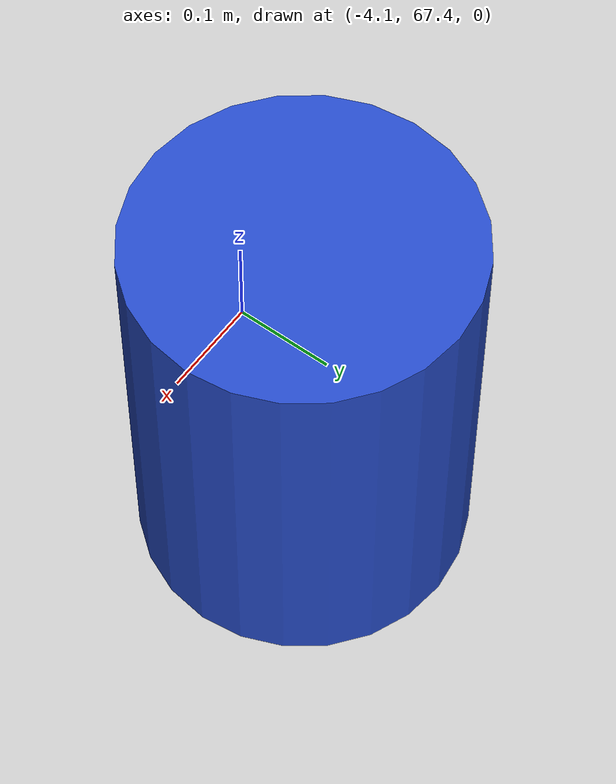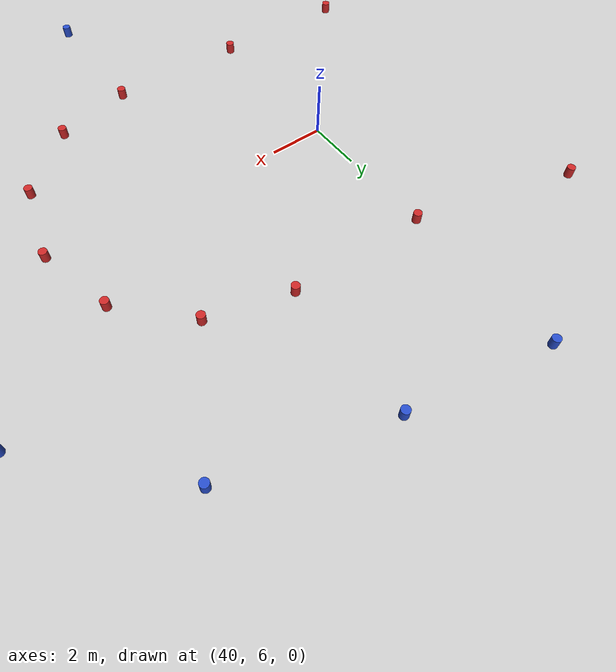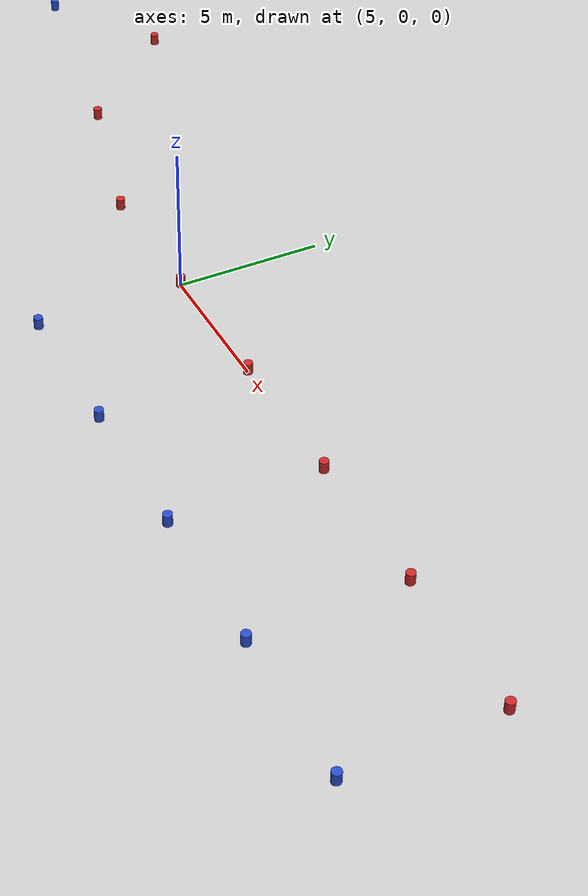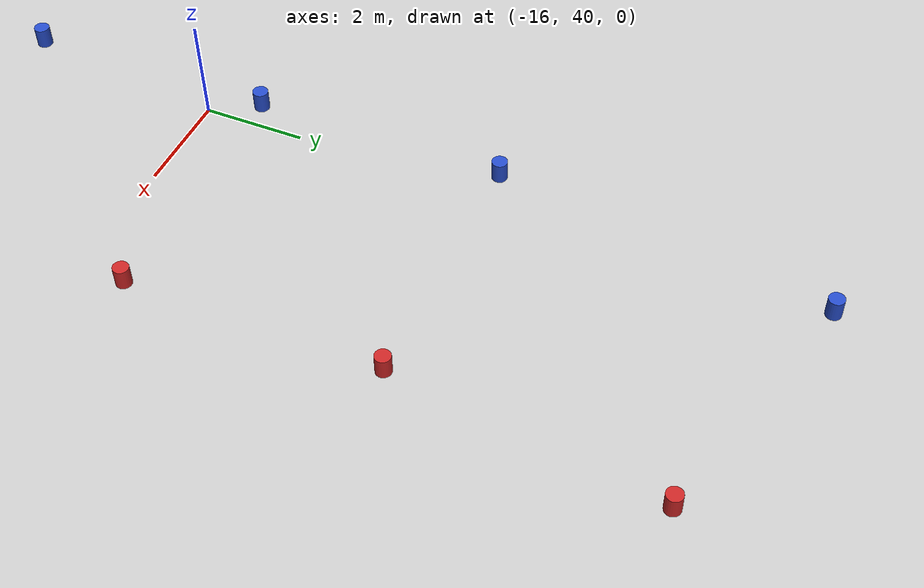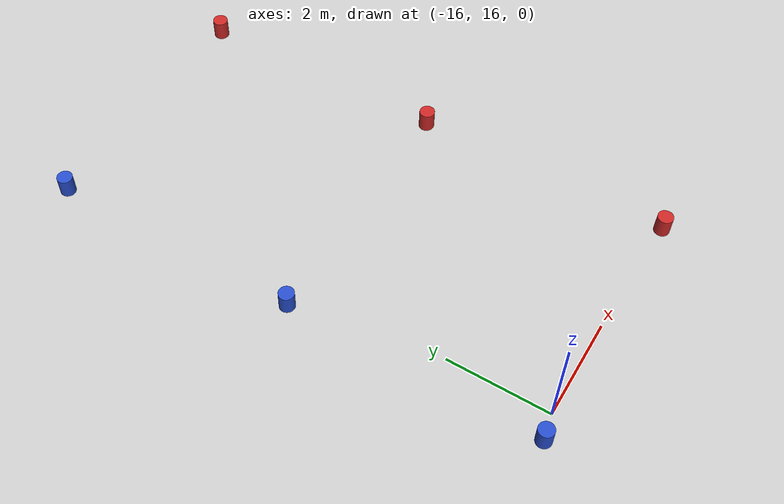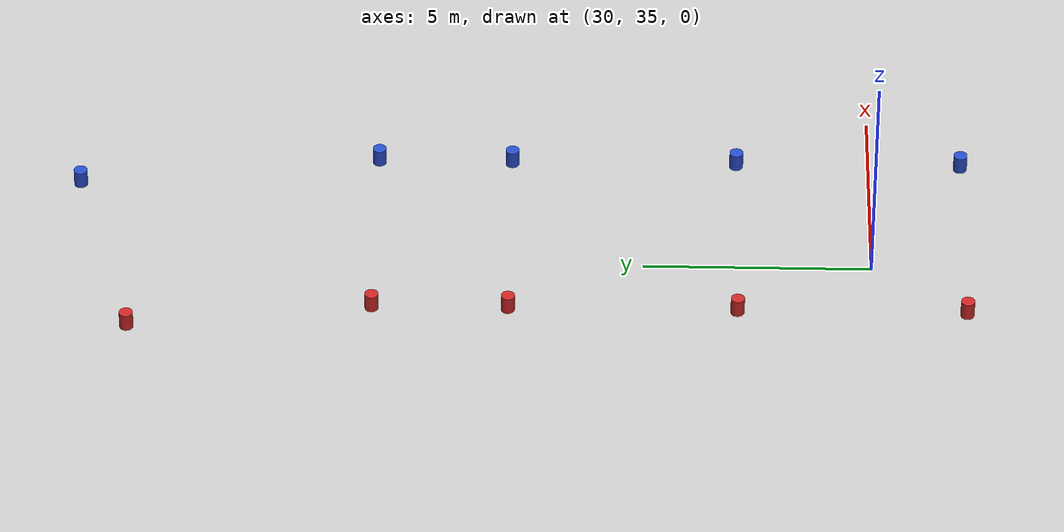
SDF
<?xml version="1.0" ?>
<sdf version="1.6">
  <world name="default">

    <!-- A ground plane -->
    <include>
      <uri>model://ground_plane</uri>
    </include>
 <model name='unit_zt_0_1'>
      <pose frame=''>0 0 0.2 0 -0 0</pose>
      <link name='link'>
        <inertial>
          <mass>1</mass>
          <inertia>
            <ixx>0.166667</ixx>
            <ixy>0</ixy>
            <ixz>0</ixz>
            <iyy>0.166667</iyy>
            <iyz>0</iyz>
            <izz>0.166667</izz>
          </inertia>
        </inertial>
        <collision name='collision'>
          <geometry>
           <cylinder>
            <radius>0.15</radius>
            <length>0.4</length>
           </cylinder>

          </geometry>
          <max_contacts>10</max_contacts>
          <surface>
            <contact>
              <ode/>
            </contact>
            <bounce/>
            <friction>
              <torsional>
                <ode/>
              </torsional>
              <ode/>
            </friction>
          </surface>
        </collision>
        <visual name='visual'>
          <geometry>
           <cylinder>
            <radius>0.15</radius>
            <length>0.4</length>
           </cylinder>
          </geometry>
          <material>
            <script>
              <name>Gazebo/Red</name>
              <uri>file://media/materials/scripts/gazebo.material</uri>
            </script>
          </material>
        </visual>
        <self_collide>0</self_collide>
        <kinematic>0</kinematic>
        <gravity>1</gravity>
      </link>
    </model>

<model name='unit_zt_0_2'>
      <pose frame=''>5 0 0.2 0 -0 0</pose>
      <link name='link'>
        <inertial>
          <mass>1</mass>
          <inertia>
            <ixx>0.166667</ixx>
            <ixy>0</ixy>
            <ixz>0</ixz>
            <iyy>0.166667</iyy>
            <iyz>0</iyz>
            <izz>0.166667</izz>
          </inertia>
        </inertial>
        <collision name='collision'>
          <geometry>
           <cylinder>
            <radius>0.15</radius>
            <length>0.4</length>
           </cylinder>

          </geometry>
          <max_contacts>10</max_contacts>
          <surface>
            <contact>
              <ode/>
            </contact>
            <bounce/>
            <friction>
              <torsional>
                <ode/>
              </torsional>
              <ode/>
            </friction>
          </surface>
        </collision>
        <visual name='visual'>
          <geometry>
           <cylinder>
            <radius>0.15</radius>
            <length>0.4</length>
           </cylinder>
          </geometry>
          <material>
            <script>
              <name>Gazebo/Red</name>
              <uri>file://media/materials/scripts/gazebo.material</uri>
            </script>
          </material>
        </visual>
        <self_collide>0</self_collide>
        <kinematic>0</kinematic>
        <gravity>1</gravity>
      </link>
   </model>

<model name='unit_zt_0_3'>
      <pose frame=''>10 0 0.2 0 -0 0</pose>
      <link name='link'>
        <inertial>
          <mass>1</mass>
          <inertia>
            <ixx>0.166667</ixx>
            <ixy>0</ixy>
            <ixz>0</ixz>
            <iyy>0.166667</iyy>
            <iyz>0</iyz>
            <izz>0.166667</izz>
          </inertia>
        </inertial>
        <collision name='collision'>
          <geometry>
           <cylinder>
            <radius>0.15</radius>
            <length>0.4</length>
           </cylinder>

          </geometry>
          <max_contacts>10</max_contacts>
          <surface>
            <contact>
              <ode/>
            </contact>
            <bounce/>
            <friction>
              <torsional>
                <ode/>
              </torsional>
              <ode/>
            </friction>
          </surface>
        </collision>
        <visual name='visual'>
          <geometry>
           <cylinder>
            <radius>0.15</radius>
            <length>0.4</length>
           </cylinder>
          </geometry>
          <material>
            <script>
              <name>Gazebo/Red</name>
              <uri>file://media/materials/scripts/gazebo.material</uri>
            </script>
          </material>
        </visual>
        <self_collide>0</self_collide>
        <kinematic>0</kinematic>
        <gravity>1</gravity>
      </link>
   </model>

<model name='unit_zt_0_4'>
      <pose frame=''>15 0 0.2 0 -0 0</pose>
      <link name='link'>
        <inertial>
          <mass>1</mass>
          <inertia>
            <ixx>0.166667</ixx>
            <ixy>0</ixy>
            <ixz>0</ixz>
            <iyy>0.166667</iyy>
            <iyz>0</iyz>
            <izz>0.166667</izz>
          </inertia>
        </inertial>
        <collision name='collision'>
          <geometry>
           <cylinder>
            <radius>0.15</radius>
            <length>0.4</length>
           </cylinder>

          </geometry>
          <max_contacts>10</max_contacts>
          <surface>
            <contact>
              <ode/>
            </contact>
            <bounce/>
            <friction>
              <torsional>
                <ode/>
              </torsional>
              <ode/>
            </friction>
          </surface>
        </collision>
        <visual name='visual'>
          <geometry>
           <cylinder>
            <radius>0.15</radius>
            <length>0.4</length>
           </cylinder>
          </geometry>
          <material>
            <script>
              <name>Gazebo/Red</name>
              <uri>file://media/materials/scripts/gazebo.material</uri>
            </script>
          </material>
        </visual>
        <self_collide>0</self_collide>
        <kinematic>0</kinematic>
        <gravity>1</gravity>
      </link>
   </model>

<model name='unit_zt_0_5'>
      <pose frame=''>20 0 0.2 0 -0 0</pose>
      <link name='link'>
        <inertial>
          <mass>1</mass>
          <inertia>
            <ixx>0.166667</ixx>
            <ixy>0</ixy>
            <ixz>0</ixz>
            <iyy>0.166667</iyy>
            <iyz>0</iyz>
            <izz>0.166667</izz>
          </inertia>
        </inertial>
        <collision name='collision'>
          <geometry>
           <cylinder>
            <radius>0.15</radius>
            <length>0.4</length>
           </cylinder>

          </geometry>
          <max_contacts>10</max_contacts>
          <surface>
            <contact>
              <ode/>
            </contact>
            <bounce/>
            <friction>
              <torsional>
                <ode/>
              </torsional>
              <ode/>
            </friction>
          </surface>
        </collision>
        <visual name='visual'>
          <geometry>
           <cylinder>
            <radius>0.15</radius>
            <length>0.4</length>
           </cylinder>
          </geometry>
          <material>
            <script>
              <name>Gazebo/Red</name>
              <uri>file://media/materials/scripts/gazebo.material</uri>
            </script>
          </material>
        </visual>
        <self_collide>0</self_collide>
        <kinematic>0</kinematic>
        <gravity>1</gravity>
      </link>
  </model>

<model name='unit_zt_0_6'>
      <pose frame=''>25 0 0.2 0 -0 0</pose>
      <link name='link'>
        <inertial>
          <mass>1</mass>
          <inertia>
            <ixx>0.166667</ixx>
            <ixy>0</ixy>
            <ixz>0</ixz>
            <iyy>0.166667</iyy>
            <iyz>0</iyz>
            <izz>0.166667</izz>
          </inertia>
        </inertial>
        <collision name='collision'>
          <geometry>
           <cylinder>
            <radius>0.15</radius>
            <length>0.4</length>
           </cylinder>

          </geometry>
          <max_contacts>10</max_contacts>
          <surface>
            <contact>
              <ode/>
            </contact>
            <bounce/>
            <friction>
              <torsional>
                <ode/>
              </torsional>
              <ode/>
            </friction>
          </surface>
        </collision>
        <visual name='visual'>
          <geometry>
           <cylinder>
            <radius>0.15</radius>
            <length>0.4</length>
           </cylinder>
          </geometry>
          <material>
            <script>
              <name>Gazebo/Red</name>
              <uri>file://media/materials/scripts/gazebo.material</uri>
            </script>
          </material>
        </visual>
        <self_collide>0</self_collide>
        <kinematic>0</kinematic>
        <gravity>1</gravity>
      </link>
   </model>

<model name='unit_zt_0_7'>
      <pose frame=''>30 0 0.2 0 -0 0</pose>
      <link name='link'>
        <inertial>
          <mass>1</mass>
          <inertia>
            <ixx>0.166667</ixx>
            <ixy>0</ixy>
            <ixz>0</ixz>
            <iyy>0.166667</iyy>
            <iyz>0</iyz>
            <izz>0.166667</izz>
          </inertia>
        </inertial>
        <collision name='collision'>
          <geometry>
           <cylinder>
            <radius>0.15</radius>
            <length>0.4</length>
           </cylinder>

          </geometry>
          <max_contacts>10</max_contacts>
          <surface>
            <contact>
              <ode/>
            </contact>
            <bounce/>
            <friction>
              <torsional>
                <ode/>
              </torsional>
              <ode/>
            </friction>
          </surface>
        </collision>
        <visual name='visual'>
          <geometry>
           <cylinder>
            <radius>0.15</radius>
            <length>0.4</length>
           </cylinder>
          </geometry>
          <material>
            <script>
              <name>Gazebo/Red</name>
              <uri>file://media/materials/scripts/gazebo.material</uri>
            </script>
          </material>
        </visual>
        <self_collide>0</self_collide>
        <kinematic>0</kinematic>
        <gravity>1</gravity>
      </link>
   </model>

<model name='unit_zt_0_8'>
      <pose frame=''>35 0 0.2 0 -0 0</pose>
      <link name='link'>
        <inertial>
          <mass>1</mass>
          <inertia>
            <ixx>0.166667</ixx>
            <ixy>0</ixy>
            <ixz>0</ixz>
            <iyy>0.166667</iyy>
            <iyz>0</iyz>
            <izz>0.166667</izz>
          </inertia>
        </inertial>
        <collision name='collision'>
          <geometry>
           <cylinder>
            <radius>0.15</radius>
            <length>0.4</length>
           </cylinder>

          </geometry>
          <max_contacts>10</max_contacts>
          <surface>
            <contact>
              <ode/>
            </contact>
            <bounce/>
            <friction>
              <torsional>
                <ode/>
              </torsional>
              <ode/>
            </friction>
          </surface>
        </collision>
        <visual name='visual'>
          <geometry>
           <cylinder>
            <radius>0.15</radius>
            <length>0.4</length>
           </cylinder>
          </geometry>
          <material>
            <script>
              <name>Gazebo/Red</name>
              <uri>file://media/materials/scripts/gazebo.material</uri>
            </script>
          </material>
        </visual>
        <self_collide>0</self_collide>
        <kinematic>0</kinematic>
        <gravity>1</gravity>
      </link>
   </model>

<model name='unit_zt_0_9'>
      <pose frame=''>40 0 0.2 0 -0 0</pose>
      <link name='link'>
        <inertial>
          <mass>1</mass>
          <inertia>
            <ixx>0.166667</ixx>
            <ixy>0</ixy>
            <ixz>0</ixz>
            <iyy>0.166667</iyy>
            <iyz>0</iyz>
            <izz>0.166667</izz>
          </inertia>
        </inertial>
        <collision name='collision'>
          <geometry>
           <cylinder>
            <radius>0.15</radius>
            <length>0.4</length>
           </cylinder>

          </geometry>
          <max_contacts>10</max_contacts>
          <surface>
            <contact>
              <ode/>
            </contact>
            <bounce/>
            <friction>
              <torsional>
                <ode/>
              </torsional>
              <ode/>
            </friction>
          </surface>
        </collision>
        <visual name='visual'>
          <geometry>
           <cylinder>
            <radius>0.15</radius>
            <length>0.4</length>
           </cylinder>
          </geometry>
          <material>
            <script>
              <name>Gazebo/Red</name>
              <uri>file://media/materials/scripts/gazebo.material</uri>
            </script>
          </material>
        </visual>
        <self_collide>0</self_collide>
        <kinematic>0</kinematic>
        <gravity>1</gravity>
      </link>
   </model>

<model name='unit_zt_0_10'>
      <pose frame=''>45 0 0.2 0 -0 0</pose>
      <link name='link'>
        <inertial>
          <mass>1</mass>
          <inertia>
            <ixx>0.166667</ixx>
            <ixy>0</ixy>
            <ixz>0</ixz>
            <iyy>0.166667</iyy>
            <iyz>0</iyz>
            <izz>0.166667</izz>
          </inertia>
        </inertial>
        <collision name='collision'>
          <geometry>
           <cylinder>
            <radius>0.15</radius>
            <length>0.4</length>
           </cylinder>

          </geometry>
          <max_contacts>10</max_contacts>
          <surface>
            <contact>
              <ode/>
            </contact>
            <bounce/>
            <friction>
              <torsional>
                <ode/>
              </torsional>
              <ode/>
            </friction>
          </surface>
        </collision>
        <visual name='visual'>
          <geometry>
           <cylinder>
            <radius>0.15</radius>
            <length>0.4</length>
           </cylinder>
          </geometry>
          <material>
            <script>
              <name>Gazebo/Red</name>
              <uri>file://media/materials/scripts/gazebo.material</uri>
            </script>
          </material>
        </visual>
        <self_collide>0</self_collide>
        <kinematic>0</kinematic>
        <gravity>1</gravity>
      </link>
   </model>

<model name='unit_zt_0_11'>
      <pose frame=''>0 -5 0.2 0 -0 0</pose>
      <link name='link'>
        <inertial>
          <mass>1</mass>
          <inertia>
            <ixx>0.166667</ixx>
            <ixy>0</ixy>
            <ixz>0</ixz>
            <iyy>0.166667</iyy>
            <iyz>0</iyz>
            <izz>0.166667</izz>
          </inertia>
        </inertial>
        <collision name='collision'>
          <geometry>
           <cylinder>
            <radius>0.15</radius>
            <length>0.4</length>
           </cylinder>

          </geometry>
          <max_contacts>10</max_contacts>
          <surface>
            <contact>
              <ode/>
            </contact>
            <bounce/>
            <friction>
              <torsional>
                <ode/>
              </torsional>
              <ode/>
            </friction>
          </surface>
        </collision>
        <visual name='visual'>
          <geometry>
           <cylinder>
            <radius>0.15</radius>
            <length>0.4</length>
           </cylinder>
          </geometry>
          <material>
            <script>
              <name>Gazebo/Blue</name>
              <uri>file://media/materials/scripts/gazebo.material</uri>
            </script>
          </material>
        </visual>
        <self_collide>0</self_collide>
        <kinematic>0</kinematic>
        <gravity>1</gravity>
      </link>
   </model>

<model name='unit_zt_0_12'>
      <pose frame=''>5 -5 0.2 0 -0 0</pose>
      <link name='link'>
        <inertial>
          <mass>1</mass>
          <inertia>
            <ixx>0.166667</ixx>
            <ixy>0</ixy>
            <ixz>0</ixz>
            <iyy>0.166667</iyy>
            <iyz>0</iyz>
            <izz>0.166667</izz>
          </inertia>
        </inertial>
        <collision name='collision'>
          <geometry>
           <cylinder>
            <radius>0.15</radius>
            <length>0.4</length>
           </cylinder>

          </geometry>
          <max_contacts>10</max_contacts>
          <surface>
            <contact>
              <ode/>
            </contact>
            <bounce/>
            <friction>
              <torsional>
                <ode/>
              </torsional>
              <ode/>
            </friction>
          </surface>
        </collision>
        <visual name='visual'>
          <geometry>
           <cylinder>
            <radius>0.15</radius>
            <length>0.4</length>
           </cylinder>
          </geometry>
          <material>
            <script>
              <name>Gazebo/Blue</name>
              <uri>file://media/materials/scripts/gazebo.material</uri>
            </script>
          </material>
        </visual>
        <self_collide>0</self_collide>
        <kinematic>0</kinematic>
        <gravity>1</gravity>
      </link>
   </model>

<model name='unit_zt_0_13'>
      <pose frame=''>10 -5 0.2 0 -0 0</pose>
      <link name='link'>
        <inertial>
          <mass>1</mass>
          <inertia>
            <ixx>0.166667</ixx>
            <ixy>0</ixy>
            <ixz>0</ixz>
            <iyy>0.166667</iyy>
            <iyz>0</iyz>
            <izz>0.166667</izz>
          </inertia>
        </inertial>
        <collision name='collision'>
          <geometry>
           <cylinder>
            <radius>0.15</radius>
            <length>0.4</length>
           </cylinder>

          </geometry>
          <max_contacts>10</max_contacts>
          <surface>
            <contact>
              <ode/>
            </contact>
            <bounce/>
            <friction>
              <torsional>
                <ode/>
              </torsional>
              <ode/>
            </friction>
          </surface>
        </collision>
        <visual name='visual'>
          <geometry>
           <cylinder>
            <radius>0.15</radius>
            <length>0.4</length>
           </cylinder>
          </geometry>
          <material>
            <script>
              <name>Gazebo/Blue</name>
              <uri>file://media/materials/scripts/gazebo.material</uri>
            </script>
          </material>
        </visual>
        <self_collide>0</self_collide>
        <kinematic>0</kinematic>
        <gravity>1</gravity>
      </link>
   </model>

<model name='unit_zt_0_14'>
      <pose frame=''>15 -5 0.2 0 -0 0</pose>
      <link name='link'>
        <inertial>
          <mass>1</mass>
          <inertia>
            <ixx>0.166667</ixx>
            <ixy>0</ixy>
            <ixz>0</ixz>
            <iyy>0.166667</iyy>
            <iyz>0</iyz>
            <izz>0.166667</izz>
          </inertia>
        </inertial>
        <collision name='collision'>
          <geometry>
           <cylinder>
            <radius>0.15</radius>
            <length>0.4</length>
           </cylinder>

          </geometry>
          <max_contacts>10</max_contacts>
          <surface>
            <contact>
              <ode/>
            </contact>
            <bounce/>
            <friction>
              <torsional>
                <ode/>
              </torsional>
              <ode/>
            </friction>
          </surface>
        </collision>
        <visual name='visual'>
          <geometry>
           <cylinder>
            <radius>0.15</radius>
            <length>0.4</length>
           </cylinder>
          </geometry>
          <material>
            <script>
              <name>Gazebo/Blue</name>
              <uri>file://media/materials/scripts/gazebo.material</uri>
            </script>
          </material>
        </visual>
        <self_collide>0</self_collide>
        <kinematic>0</kinematic>
        <gravity>1</gravity>
      </link>
   </model>

<model name='unit_zt_0_15'>
      <pose frame=''>20 -5 0.2 0 -0 0</pose>
      <link name='link'>
        <inertial>
          <mass>1</mass>
          <inertia>
            <ixx>0.166667</ixx>
            <ixy>0</ixy>
            <ixz>0</ixz>
            <iyy>0.166667</iyy>
            <iyz>0</iyz>
            <izz>0.166667</izz>
          </inertia>
        </inertial>
        <collision name='collision'>
          <geometry>
           <cylinder>
            <radius>0.15</radius>
            <length>0.4</length>
           </cylinder>

          </geometry>
          <max_contacts>10</max_contacts>
          <surface>
            <contact>
              <ode/>
            </contact>
            <bounce/>
            <friction>
              <torsional>
                <ode/>
              </torsional>
              <ode/>
            </friction>
          </surface>
        </collision>
        <visual name='visual'>
          <geometry>
           <cylinder>
            <radius>0.15</radius>
            <length>0.4</length>
           </cylinder>
          </geometry>
          <material>
            <script>
              <name>Gazebo/Blue</name>
              <uri>file://media/materials/scripts/gazebo.material</uri>
            </script>
          </material>
        </visual>
        <self_collide>0</self_collide>
        <kinematic>0</kinematic>
        <gravity>1</gravity>
      </link>
   </model>

<model name='unit_zt_0_16'>
      <pose frame=''>20 -5 0.2 0 -0 0</pose>
      <link name='link'>
        <inertial>
          <mass>1</mass>
          <inertia>
            <ixx>0.166667</ixx>
            <ixy>0</ixy>
            <ixz>0</ixz>
            <iyy>0.166667</iyy>
            <iyz>0</iyz>
            <izz>0.166667</izz>
          </inertia>
        </inertial>
        <collision name='collision'>
          <geometry>
           <cylinder>
            <radius>0.15</radius>
            <length>0.4</length>
           </cylinder>

          </geometry>
          <max_contacts>10</max_contacts>
          <surface>
            <contact>
              <ode/>
            </contact>
            <bounce/>
            <friction>
              <torsional>
                <ode/>
              </torsional>
              <ode/>
            </friction>
          </surface>
        </collision>
        <visual name='visual'>
          <geometry>
           <cylinder>
            <radius>0.15</radius>
            <length>0.4</length>
           </cylinder>
          </geometry>
          <material>
            <script>
              <name>Gazebo/Blue</name>
              <uri>file://media/materials/scripts/gazebo.material</uri>
            </script>
          </material>
        </visual>
        <self_collide>0</self_collide>
        <kinematic>0</kinematic>
        <gravity>1</gravity>
      </link>
   </model>

<model name='unit_zt_0_17'>
      <pose frame=''>25 -5 0.2 0 -0 0</pose>
      <link name='link'>
        <inertial>
          <mass>1</mass>
          <inertia>
            <ixx>0.166667</ixx>
            <ixy>0</ixy>
            <ixz>0</ixz>
            <iyy>0.166667</iyy>
            <iyz>0</iyz>
            <izz>0.166667</izz>
          </inertia>
        </inertial>
        <collision name='collision'>
          <geometry>
           <cylinder>
            <radius>0.15</radius>
            <length>0.4</length>
           </cylinder>

          </geometry>
          <max_contacts>10</max_contacts>
          <surface>
            <contact>
              <ode/>
            </contact>
            <bounce/>
            <friction>
              <torsional>
                <ode/>
              </torsional>
              <ode/>
            </friction>
          </surface>
        </collision>
        <visual name='visual'>
          <geometry>
           <cylinder>
            <radius>0.15</radius>
            <length>0.4</length>
           </cylinder>
          </geometry>
          <material>
            <script>
              <name>Gazebo/Blue</name>
              <uri>file://media/materials/scripts/gazebo.material</uri>
            </script>
          </material>
        </visual>
        <self_collide>0</self_collide>
        <kinematic>0</kinematic>
        <gravity>1</gravity>
      </link>
   </model>

<model name='unit_zt_0_18'>
      <pose frame=''>30 -5 0.2 0 -0 0</pose>
      <link name='link'>
        <inertial>
          <mass>1</mass>
          <inertia>
            <ixx>0.166667</ixx>
            <ixy>0</ixy>
            <ixz>0</ixz>
            <iyy>0.166667</iyy>
            <iyz>0</iyz>
            <izz>0.166667</izz>
          </inertia>
        </inertial>
        <collision name='collision'>
          <geometry>
           <cylinder>
            <radius>0.15</radius>
            <length>0.4</length>
           </cylinder>

          </geometry>
          <max_contacts>10</max_contacts>
          <surface>
            <contact>
              <ode/>
            </contact>
            <bounce/>
            <friction>
              <torsional>
                <ode/>
              </torsional>
              <ode/>
            </friction>
          </surface>
        </collision>
        <visual name='visual'>
          <geometry>
           <cylinder>
            <radius>0.15</radius>
            <length>0.4</length>
           </cylinder>
          </geometry>
          <material>
            <script>
              <name>Gazebo/Blue</name>
              <uri>file://media/materials/scripts/gazebo.material</uri>
            </script>
          </material>
        </visual>
        <self_collide>0</self_collide>
        <kinematic>0</kinematic>
        <gravity>1</gravity>
      </link>
   </model>

<model name='unit_zt_0_19'>
      <pose frame=''>35 -5 0.2 0 -0 0</pose>
      <link name='link'>
        <inertial>
          <mass>1</mass>
          <inertia>
            <ixx>0.166667</ixx>
            <ixy>0</ixy>
            <ixz>0</ixz>
            <iyy>0.166667</iyy>
            <iyz>0</iyz>
            <izz>0.166667</izz>
          </inertia>
        </inertial>
        <collision name='collision'>
          <geometry>
           <cylinder>
            <radius>0.15</radius>
            <length>0.4</length>
           </cylinder>

          </geometry>
          <max_contacts>10</max_contacts>
          <surface>
            <contact>
              <ode/>
            </contact>
            <bounce/>
            <friction>
              <torsional>
                <ode/>
              </torsional>
              <ode/>
            </friction>
          </surface>
        </collision>
        <visual name='visual'>
          <geometry>
           <cylinder>
            <radius>0.15</radius>
            <length>0.4</length>
           </cylinder>
          </geometry>
          <material>
            <script>
              <name>Gazebo/Blue</name>
              <uri>file://media/materials/scripts/gazebo.material</uri>
            </script>
          </material>
        </visual>
        <self_collide>0</self_collide>
        <kinematic>0</kinematic>
        <gravity>1</gravity>
      </link>
   </model>

<model name='unit_zt_0_20'>
      <pose frame=''>40 -5 0.2 0 -0 0</pose>
      <link name='link'>
        <inertial>
          <mass>1</mass>
          <inertia>
            <ixx>0.166667</ixx>
            <ixy>0</ixy>
            <ixz>0</ixz>
            <iyy>0.166667</iyy>
            <iyz>0</iyz>
            <izz>0.166667</izz>
          </inertia>
        </inertial>
        <collision name='collision'>
          <geometry>
           <cylinder>
            <radius>0.15</radius>
            <length>0.4</length>
           </cylinder>

          </geometry>
          <max_contacts>10</max_contacts>
          <surface>
            <contact>
              <ode/>
            </contact>
            <bounce/>
            <friction>
              <torsional>
                <ode/>
              </torsional>
              <ode/>
            </friction>
          </surface>
        </collision>
        <visual name='visual'>
          <geometry>
           <cylinder>
            <radius>0.15</radius>
            <length>0.4</length>
           </cylinder>
          </geometry>
          <material>
            <script>
              <name>Gazebo/Blue</name>
              <uri>file://media/materials/scripts/gazebo.material</uri>
            </script>
          </material>
        </visual>
        <self_collide>0</self_collide>
        <kinematic>0</kinematic>
        <gravity>1</gravity>
      </link>
   </model>

<model name='unit_zt_0_21'>
      <pose frame=''>45 -5 0.2 0 -0 0</pose>
      <link name='link'>
        <inertial>
          <mass>1</mass>
          <inertia>
            <ixx>0.166667</ixx>
            <ixy>0</ixy>
            <ixz>0</ixz>
            <iyy>0.166667</iyy>
            <iyz>0</iyz>
            <izz>0.166667</izz>
          </inertia>
        </inertial>
        <collision name='collision'>
          <geometry>
           <cylinder>
            <radius>0.15</radius>
            <length>0.4</length>
           </cylinder>

          </geometry>
          <max_contacts>10</max_contacts>
          <surface>
            <contact>
              <ode/>
            </contact>
            <bounce/>
            <friction>
              <torsional>
                <ode/>
              </torsional>
              <ode/>
            </friction>
          </surface>
        </collision>
        <visual name='visual'>
          <geometry>
           <cylinder>
            <radius>0.15</radius>
            <length>0.4</length>
           </cylinder>
          </geometry>
          <material>
            <script>
              <name>Gazebo/Blue</name>
              <uri>file://media/materials/scripts/gazebo.material</uri>
            </script>
          </material>
        </visual>
        <self_collide>0</self_collide>
        <kinematic>0</kinematic>
        <gravity>1</gravity>
      </link>
   </model>

<model name='unit_zt_0_22'>
      <pose frame=''>47.8 0.75 0.2 0 -0 0</pose>
      <link name='link'>
        <inertial>
          <mass>1</mass>
          <inertia>
            <ixx>0.166667</ixx>
            <ixy>0</ixy>
            <ixz>0</ixz>
            <iyy>0.166667</iyy>
            <iyz>0</iyz>
            <izz>0.166667</izz>
          </inertia>
        </inertial>
        <collision name='collision'>
          <geometry>
           <cylinder>
            <radius>0.15</radius>
            <length>0.4</length>
           </cylinder>

          </geometry>
          <max_contacts>10</max_contacts>
          <surface>
            <contact>
              <ode/>
            </contact>
            <bounce/>
            <friction>
              <torsional>
                <ode/>
              </torsional>
              <ode/>
            </friction>
          </surface>
        </collision>
        <visual name='visual'>
          <geometry>
           <cylinder>
            <radius>0.15</radius>
            <length>0.4</length>
           </cylinder>
          </geometry>
          <material>
            <script>
              <name>Gazebo/Red</name>
              <uri>file://media/materials/scripts/gazebo.material</uri>
            </script>
          </material>
        </visual>
        <self_collide>0</self_collide>
        <kinematic>0</kinematic>
        <gravity>1</gravity>
      </link>
   </model>

<model name='unit_zt_0_23'>
      <pose frame=''>50 2.86 0.2 0 -0 0</pose>
      <link name='link'>
        <inertial>
          <mass>1</mass>
          <inertia>
            <ixx>0.166667</ixx>
            <ixy>0</ixy>
            <ixz>0</ixz>
            <iyy>0.166667</iyy>
            <iyz>0</iyz>
            <izz>0.166667</izz>
          </inertia>
        </inertial>
        <collision name='collision'>
          <geometry>
           <cylinder>
            <radius>0.15</radius>
            <length>0.4</length>
           </cylinder>

          </geometry>
          <max_contacts>10</max_contacts>
          <surface>
            <contact>
              <ode/>
            </contact>
            <bounce/>
            <friction>
              <torsional>
                <ode/>
              </torsional>
              <ode/>
            </friction>
          </surface>
        </collision>
        <visual name='visual'>
          <geometry>
           <cylinder>
            <radius>0.15</radius>
            <length>0.4</length>
           </cylinder>
          </geometry>
          <material>
            <script>
              <name>Gazebo/Red</name>
              <uri>file://media/materials/scripts/gazebo.material</uri>
            </script>
          </material>
        </visual>
        <self_collide>0</self_collide>
        <kinematic>0</kinematic>
        <gravity>1</gravity>
      </link>
   </model>

<model name='unit_zt_0_24'>
      <pose frame=''>50.71 5.72 0.2 0 -0 0</pose>
      <link name='link'>
        <inertial>
          <mass>1</mass>
          <inertia>
            <ixx>0.166667</ixx>
            <ixy>0</ixy>
            <ixz>0</ixz>
            <iyy>0.166667</iyy>
            <iyz>0</iyz>
            <izz>0.166667</izz>
          </inertia>
        </inertial>
        <collision name='collision'>
          <geometry>
           <cylinder>
            <radius>0.15</radius>
            <length>0.4</length>
           </cylinder>

          </geometry>
          <max_contacts>10</max_contacts>
          <surface>
            <contact>
              <ode/>
            </contact>
            <bounce/>
            <friction>
              <torsional>
                <ode/>
              </torsional>
              <ode/>
            </friction>
          </surface>
        </collision>
        <visual name='visual'>
          <geometry>
           <cylinder>
            <radius>0.15</radius>
            <length>0.4</length>
           </cylinder>
          </geometry>
          <material>
            <script>
              <name>Gazebo/Red</name>
              <uri>file://media/materials/scripts/gazebo.material</uri>
            </script>
          </material>
        </visual>
        <self_collide>0</self_collide>
        <kinematic>0</kinematic>
        <gravity>1</gravity>
      </link>
   </model>

<model name='unit_zt_0_25'>
      <pose frame=''>49.97 8.54 0.2 0 -0 0</pose>
      <link name='link'>
        <inertial>
          <mass>1</mass>
          <inertia>
            <ixx>0.166667</ixx>
            <ixy>0</ixy>
            <ixz>0</ixz>
            <iyy>0.166667</iyy>
            <iyz>0</iyz>
            <izz>0.166667</izz>
          </inertia>
        </inertial>
        <collision name='collision'>
          <geometry>
           <cylinder>
            <radius>0.15</radius>
            <length>0.4</length>
           </cylinder>

          </geometry>
          <max_contacts>10</max_contacts>
          <surface>
            <contact>
              <ode/>
            </contact>
            <bounce/>
            <friction>
              <torsional>
                <ode/>
              </torsional>
              <ode/>
            </friction>
          </surface>
        </collision>
        <visual name='visual'>
          <geometry>
           <cylinder>
            <radius>0.15</radius>
            <length>0.4</length>
           </cylinder>
          </geometry>
          <material>
            <script>
              <name>Gazebo/Red</name>
              <uri>file://media/materials/scripts/gazebo.material</uri>
            </script>
          </material>
        </visual>
        <self_collide>0</self_collide>
        <kinematic>0</kinematic>
        <gravity>1</gravity>
      </link>
   </model>

<model name='unit_zt_0_26'>
      <pose frame=''>47.89 10.66 0.2 0 -0 0</pose>
      <link name='link'>
        <inertial>
          <mass>1</mass>
          <inertia>
            <ixx>0.166667</ixx>
            <ixy>0</ixy>
            <ixz>0</ixz>
            <iyy>0.166667</iyy>
            <iyz>0</iyz>
            <izz>0.166667</izz>
          </inertia>
        </inertial>
        <collision name='collision'>
          <geometry>
           <cylinder>
            <radius>0.15</radius>
            <length>0.4</length>
           </cylinder>

          </geometry>
          <max_contacts>10</max_contacts>
          <surface>
            <contact>
              <ode/>
            </contact>
            <bounce/>
            <friction>
              <torsional>
                <ode/>
              </torsional>
              <ode/>
            </friction>
          </surface>
        </collision>
        <visual name='visual'>
          <geometry>
           <cylinder>
            <radius>0.15</radius>
            <length>0.4</length>
           </cylinder>
          </geometry>
          <material>
            <script>
              <name>Gazebo/Red</name>
              <uri>file://media/materials/scripts/gazebo.material</uri>
            </script>
          </material>
        </visual>
        <self_collide>0</self_collide>
        <kinematic>0</kinematic>
        <gravity>1</gravity>
      </link>
   </model>

<model name='unit_zt_0_27'>
      <pose frame=''>45 11.44 0.2 0 -0 0</pose>
      <link name='link'>
        <inertial>
          <mass>1</mass>
          <inertia>
            <ixx>0.166667</ixx>
            <ixy>0</ixy>
            <ixz>0</ixz>
            <iyy>0.166667</iyy>
            <iyz>0</iyz>
            <izz>0.166667</izz>
          </inertia>
        </inertial>
        <collision name='collision'>
          <geometry>
           <cylinder>
            <radius>0.15</radius>
            <length>0.4</length>
           </cylinder>

          </geometry>
          <max_contacts>10</max_contacts>
          <surface>
            <contact>
              <ode/>
            </contact>
            <bounce/>
            <friction>
              <torsional>
                <ode/>
              </torsional>
              <ode/>
            </friction>
          </surface>
        </collision>
        <visual name='visual'>
          <geometry>
           <cylinder>
            <radius>0.15</radius>
            <length>0.4</length>
           </cylinder>
          </geometry>
          <material>
            <script>
              <name>Gazebo/Red</name>
              <uri>file://media/materials/scripts/gazebo.material</uri>
            </script>
          </material>
        </visual>
        <self_collide>0</self_collide>
        <kinematic>0</kinematic>
        <gravity>1</gravity>
      </link>
   </model>

<model name='unit_zt_0_28'>
      <pose frame=''>50.31 -3.59 0.2 0 -0 0</pose>
      <link name='link'>
        <inertial>
          <mass>1</mass>
          <inertia>
            <ixx>0.166667</ixx>
            <ixy>0</ixy>
            <ixz>0</ixz>
            <iyy>0.166667</iyy>
            <iyz>0</iyz>
            <izz>0.166667</izz>
          </inertia>
        </inertial>
        <collision name='collision'>
          <geometry>
           <cylinder>
            <radius>0.15</radius>
            <length>0.4</length>
           </cylinder>

          </geometry>
          <max_contacts>10</max_contacts>
          <surface>
            <contact>
              <ode/>
            </contact>
            <bounce/>
            <friction>
              <torsional>
                <ode/>
              </torsional>
              <ode/>
            </friction>
          </surface>
        </collision>
        <visual name='visual'>
          <geometry>
           <cylinder>
            <radius>0.15</radius>
            <length>0.4</length>
           </cylinder>
          </geometry>
          <material>
            <script>
              <name>Gazebo/Blue</name>
              <uri>file://media/materials/scripts/gazebo.material</uri>
            </script>
          </material>
        </visual>
        <self_collide>0</self_collide>
        <kinematic>0</kinematic>
        <gravity>1</gravity>
      </link>
   </model>

<model name='unit_zt_0_29'>
      <pose frame=''>54.29 0.37 0.2 0 -0 0</pose>
      <link name='link'>
        <inertial>
          <mass>1</mass>
          <inertia>
            <ixx>0.166667</ixx>
            <ixy>0</ixy>
            <ixz>0</ixz>
            <iyy>0.166667</iyy>
            <iyz>0</iyz>
            <izz>0.166667</izz>
          </inertia>
        </inertial>
        <collision name='collision'>
          <geometry>
           <cylinder>
            <radius>0.15</radius>
            <length>0.4</length>
           </cylinder>

          </geometry>
          <max_contacts>10</max_contacts>
          <surface>
            <contact>
              <ode/>
            </contact>
            <bounce/>
            <friction>
              <torsional>
                <ode/>
              </torsional>
              <ode/>
            </friction>
          </surface>
        </collision>
        <visual name='visual'>
          <geometry>
           <cylinder>
            <radius>0.15</radius>
            <length>0.4</length>
           </cylinder>
          </geometry>
          <material>
            <script>
              <name>Gazebo/Blue</name>
              <uri>file://media/materials/scripts/gazebo.material</uri>
            </script>
          </material>
        </visual>
        <self_collide>0</self_collide>
        <kinematic>0</kinematic>
        <gravity>1</gravity>
      </link>
   </model>

<model name='unit_zt_0_30'>
      <pose frame=''>55.72 5.72 0.2 0 -0 0</pose>
      <link name='link'>
        <inertial>
          <mass>1</mass>
          <inertia>
            <ixx>0.166667</ixx>
            <ixy>0</ixy>
            <ixz>0</ixz>
            <iyy>0.166667</iyy>
            <iyz>0</iyz>
            <izz>0.166667</izz>
          </inertia>
        </inertial>
        <collision name='collision'>
          <geometry>
           <cylinder>
            <radius>0.15</radius>
            <length>0.4</length>
           </cylinder>

          </geometry>
          <max_contacts>10</max_contacts>
          <surface>
            <contact>
              <ode/>
            </contact>
            <bounce/>
            <friction>
              <torsional>
                <ode/>
              </torsional>
              <ode/>
            </friction>
          </surface>
        </collision>
        <visual name='visual'>
          <geometry>
           <cylinder>
            <radius>0.15</radius>
            <length>0.4</length>
           </cylinder>
          </geometry>
          <material>
            <script>
              <name>Gazebo/Blue</name>
              <uri>file://media/materials/scripts/gazebo.material</uri>
            </script>
          </material>
        </visual>
        <self_collide>0</self_collide>
        <kinematic>0</kinematic>
        <gravity>1</gravity>
      </link>
   </model>

<model name='unit_zt_0_31'>
      <pose frame=''>54.32 11.01 0.2 0 -0 0</pose>
      <link name='link'>
        <inertial>
          <mass>1</mass>
          <inertia>
            <ixx>0.166667</ixx>
            <ixy>0</ixy>
            <ixz>0</ixz>
            <iyy>0.166667</iyy>
            <iyz>0</iyz>
            <izz>0.166667</izz>
          </inertia>
        </inertial>
        <collision name='collision'>
          <geometry>
           <cylinder>
            <radius>0.15</radius>
            <length>0.4</length>
           </cylinder>

          </geometry>
          <max_contacts>10</max_contacts>
          <surface>
            <contact>
              <ode/>
            </contact>
            <bounce/>
            <friction>
              <torsional>
                <ode/>
              </torsional>
              <ode/>
            </friction>
          </surface>
        </collision>
        <visual name='visual'>
          <geometry>
           <cylinder>
            <radius>0.15</radius>
            <length>0.4</length>
           </cylinder>
          </geometry>
          <material>
            <script>
              <name>Gazebo/Blue</name>
              <uri>file://media/materials/scripts/gazebo.material</uri>
            </script>
          </material>
        </visual>
        <self_collide>0</self_collide>
        <kinematic>0</kinematic>
        <gravity>1</gravity>
      </link>
   </model>

<model name='unit_zt_0_32'>
      <pose frame=''>50.41 14.97 0.2 0 -0 0</pose>
      <link name='link'>
        <inertial>
          <mass>1</mass>
          <inertia>
            <ixx>0.166667</ixx>
            <ixy>0</ixy>
            <ixz>0</ixz>
            <iyy>0.166667</iyy>
            <iyz>0</iyz>
            <izz>0.166667</izz>
          </inertia>
        </inertial>
        <collision name='collision'>
          <geometry>
           <cylinder>
            <radius>0.15</radius>
            <length>0.4</length>
           </cylinder>

          </geometry>
          <max_contacts>10</max_contacts>
          <surface>
            <contact>
              <ode/>
            </contact>
            <bounce/>
            <friction>
              <torsional>
                <ode/>
              </torsional>
              <ode/>
            </friction>
          </surface>
        </collision>
        <visual name='visual'>
          <geometry>
           <cylinder>
            <radius>0.15</radius>
            <length>0.4</length>
           </cylinder>
          </geometry>
          <material>
            <script>
              <name>Gazebo/Blue</name>
              <uri>file://media/materials/scripts/gazebo.material</uri>
            </script>
          </material>
        </visual>
        <self_collide>0</self_collide>
        <kinematic>0</kinematic>
        <gravity>1</gravity>
      </link>
   </model>

<model name='unit_zt_0_33'>
      <pose frame=''>45 16.44 0.2 0 -0 0</pose>
      <link name='link'>
        <inertial>
          <mass>1</mass>
          <inertia>
            <ixx>0.166667</ixx>
            <ixy>0</ixy>
            <ixz>0</ixz>
            <iyy>0.166667</iyy>
            <iyz>0</iyz>
            <izz>0.166667</izz>
          </inertia>
        </inertial>
        <collision name='collision'>
          <geometry>
           <cylinder>
            <radius>0.15</radius>
            <length>0.4</length>
           </cylinder>

          </geometry>
          <max_contacts>10</max_contacts>
          <surface>
            <contact>
              <ode/>
            </contact>
            <bounce/>
            <friction>
              <torsional>
                <ode/>
              </torsional>
              <ode/>
            </friction>
          </surface>
        </collision>
        <visual name='visual'>
          <geometry>
           <cylinder>
            <radius>0.15</radius>
            <length>0.4</length>
           </cylinder>
          </geometry>
          <material>
            <script>
              <name>Gazebo/Blue</name>
              <uri>file://media/materials/scripts/gazebo.material</uri>
            </script>
          </material>
        </visual>
        <self_collide>0</self_collide>
        <kinematic>0</kinematic>
        <gravity>1</gravity>
      </link>
   </model>

<model name='unit_zt_0_34'>
      <pose frame=''>40 11.44 0.2 0 -0 0</pose>
      <link name='link'>
        <inertial>
          <mass>1</mass>
          <inertia>
            <ixx>0.166667</ixx>
            <ixy>0</ixy>
            <ixz>0</ixz>
            <iyy>0.166667</iyy>
            <iyz>0</iyz>
            <izz>0.166667</izz>
          </inertia>
        </inertial>
        <collision name='collision'>
          <geometry>
           <cylinder>
            <radius>0.15</radius>
            <length>0.4</length>
           </cylinder>

          </geometry>
          <max_contacts>10</max_contacts>
          <surface>
            <contact>
              <ode/>
            </contact>
            <bounce/>
            <friction>
              <torsional>
                <ode/>
              </torsional>
              <ode/>
            </friction>
          </surface>
        </collision>
        <visual name='visual'>
          <geometry>
           <cylinder>
            <radius>0.15</radius>
            <length>0.4</length>
           </cylinder>
          </geometry>
          <material>
            <script>
              <name>Gazebo/Red</name>
              <uri>file://media/materials/scripts/gazebo.material</uri>
            </script>
          </material>
        </visual>
        <self_collide>0</self_collide>
        <kinematic>0</kinematic>
        <gravity>1</gravity>
      </link>
   </model>

<model name='unit_zt_0_35'>
      <pose frame=''>34.22 13 0.2 0 -0 0</pose>
      <link name='link'>
        <inertial>
          <mass>1</mass>
          <inertia>
            <ixx>0.166667</ixx>
            <ixy>0</ixy>
            <ixz>0</ixz>
            <iyy>0.166667</iyy>
            <iyz>0</iyz>
            <izz>0.166667</izz>
          </inertia>
        </inertial>
        <collision name='collision'>
          <geometry>
           <cylinder>
            <radius>0.15</radius>
            <length>0.4</length>
           </cylinder>

          </geometry>
          <max_contacts>10</max_contacts>
          <surface>
            <contact>
              <ode/>
            </contact>
            <bounce/>
            <friction>
              <torsional>
                <ode/>
              </torsional>
              <ode/>
            </friction>
          </surface>
        </collision>
        <visual name='visual'>
          <geometry>
           <cylinder>
            <radius>0.15</radius>
            <length>0.4</length>
           </cylinder>
          </geometry>
          <material>
            <script>
              <name>Gazebo/Red</name>
              <uri>file://media/materials/scripts/gazebo.material</uri>
            </script>
          </material>
        </visual>
        <self_collide>0</self_collide>
        <kinematic>0</kinematic>
        <gravity>1</gravity>
      </link>
   </model>

<model name='unit_zt_0_36'>
      <pose frame=''>30.51 16.44 0.2 0 -0 0</pose>
      <link name='link'>
        <inertial>
          <mass>1</mass>
          <inertia>
            <ixx>0.166667</ixx>
            <ixy>0</ixy>
            <ixz>0</ixz>
            <iyy>0.166667</iyy>
            <iyz>0</iyz>
            <izz>0.166667</izz>
          </inertia>
        </inertial>
        <collision name='collision'>
          <geometry>
           <cylinder>
            <radius>0.15</radius>
            <length>0.4</length>
           </cylinder>

          </geometry>
          <max_contacts>10</max_contacts>
          <surface>
            <contact>
              <ode/>
            </contact>
            <bounce/>
            <friction>
              <torsional>
                <ode/>
              </torsional>
              <ode/>
            </friction>
          </surface>
        </collision>
        <visual name='visual'>
          <geometry>
           <cylinder>
            <radius>0.15</radius>
            <length>0.4</length>
           </cylinder>
          </geometry>
          <material>
            <script>
              <name>Gazebo/Red</name>
              <uri>file://media/materials/scripts/gazebo.material</uri>
            </script>
          </material>
        </visual>
        <self_collide>0</self_collide>
        <kinematic>0</kinematic>
        <gravity>1</gravity>
      </link>
   </model>

<model name='unit_zt_0_37'>
      <pose frame=''>28.5 22.94 0.2 0 -0 0</pose>
      <link name='link'>
        <inertial>
          <mass>1</mass>
          <inertia>
            <ixx>0.166667</ixx>
            <ixy>0</ixy>
            <ixz>0</ixz>
            <iyy>0.166667</iyy>
            <iyz>0</iyz>
            <izz>0.166667</izz>
          </inertia>
        </inertial>
        <collision name='collision'>
          <geometry>
           <cylinder>
            <radius>0.15</radius>
            <length>0.4</length>
           </cylinder>

          </geometry>
          <max_contacts>10</max_contacts>
          <surface>
            <contact>
              <ode/>
            </contact>
            <bounce/>
            <friction>
              <torsional>
                <ode/>
              </torsional>
              <ode/>
            </friction>
          </surface>
        </collision>
        <visual name='visual'>
          <geometry>
           <cylinder>
            <radius>0.15</radius>
            <length>0.4</length>
           </cylinder>
          </geometry>
          <material>
            <script>
              <name>Gazebo/Red</name>
              <uri>file://media/materials/scripts/gazebo.material</uri>
            </script>
          </material>
        </visual>
        <self_collide>0</self_collide>
        <kinematic>0</kinematic>
        <gravity>1</gravity>
      </link>
   </model>

<model name='unit_zt_0_38'>
      <pose frame=''>28.5 27.94 0.2 0 -0 0</pose>
      <link name='link'>
        <inertial>
          <mass>1</mass>
          <inertia>
            <ixx>0.166667</ixx>
            <ixy>0</ixy>
            <ixz>0</ixz>
            <iyy>0.166667</iyy>
            <iyz>0</iyz>
            <izz>0.166667</izz>
          </inertia>
        </inertial>
        <collision name='collision'>
          <geometry>
           <cylinder>
            <radius>0.15</radius>
            <length>0.4</length>
           </cylinder>

          </geometry>
          <max_contacts>10</max_contacts>
          <surface>
            <contact>
              <ode/>
            </contact>
            <bounce/>
            <friction>
              <torsional>
                <ode/>
              </torsional>
              <ode/>
            </friction>
          </surface>
        </collision>
        <visual name='visual'>
          <geometry>
           <cylinder>
            <radius>0.15</radius>
            <length>0.4</length>
           </cylinder>
          </geometry>
          <material>
            <script>
              <name>Gazebo/Red</name>
              <uri>file://media/materials/scripts/gazebo.material</uri>
            </script>
          </material>
        </visual>
        <self_collide>0</self_collide>
        <kinematic>0</kinematic>
        <gravity>1</gravity>
      </link>
   </model>

<model name='unit_zt_0_39'>
      <pose frame=''>28.5 32.94 0.2 0 -0 0</pose>
      <link name='link'>
        <inertial>
          <mass>1</mass>
          <inertia>
            <ixx>0.166667</ixx>
            <ixy>0</ixy>
            <ixz>0</ixz>
            <iyy>0.166667</iyy>
            <iyz>0</iyz>
            <izz>0.166667</izz>
          </inertia>
        </inertial>
        <collision name='collision'>
          <geometry>
           <cylinder>
            <radius>0.15</radius>
            <length>0.4</length>
           </cylinder>

          </geometry>
          <max_contacts>10</max_contacts>
          <surface>
            <contact>
              <ode/>
            </contact>
            <bounce/>
            <friction>
              <torsional>
                <ode/>
              </torsional>
              <ode/>
            </friction>
          </surface>
        </collision>
        <visual name='visual'>
          <geometry>
           <cylinder>
            <radius>0.15</radius>
            <length>0.4</length>
           </cylinder>
          </geometry>
          <material>
            <script>
              <name>Gazebo/Red</name>
              <uri>file://media/materials/scripts/gazebo.material</uri>
            </script>
          </material>
        </visual>
        <self_collide>0</self_collide>
        <kinematic>0</kinematic>
        <gravity>1</gravity>
      </link>
   </model>

<model name='unit_zt_0_40'>
      <pose frame=''>28.5 37.94 0.2 0 -0 0</pose>
      <link name='link'>
        <inertial>
          <mass>1</mass>
          <inertia>
            <ixx>0.166667</ixx>
            <ixy>0</ixy>
            <ixz>0</ixz>
            <iyy>0.166667</iyy>
            <iyz>0</iyz>
            <izz>0.166667</izz>
          </inertia>
        </inertial>
        <collision name='collision'>
          <geometry>
           <cylinder>
            <radius>0.15</radius>
            <length>0.4</length>
           </cylinder>

          </geometry>
          <max_contacts>10</max_contacts>
          <surface>
            <contact>
              <ode/>
            </contact>
            <bounce/>
            <friction>
              <torsional>
                <ode/>
              </torsional>
              <ode/>
            </friction>
          </surface>
        </collision>
        <visual name='visual'>
          <geometry>
           <cylinder>
            <radius>0.15</radius>
            <length>0.4</length>
           </cylinder>
          </geometry>
          <material>
            <script>
              <name>Gazebo/Red</name>
              <uri>file://media/materials/scripts/gazebo.material</uri>
            </script>
          </material>
        </visual>
        <self_collide>0</self_collide>
        <kinematic>0</kinematic>
        <gravity>1</gravity>
      </link>
   </model>

<model name='unit_zt_0_41'>
      <pose frame=''>28.5 42.94 0.2 0 -0 0</pose>
      <link name='link'>
        <inertial>
          <mass>1</mass>
          <inertia>
            <ixx>0.166667</ixx>
            <ixy>0</ixy>
            <ixz>0</ixz>
            <iyy>0.166667</iyy>
            <iyz>0</iyz>
            <izz>0.166667</izz>
          </inertia>
        </inertial>
        <collision name='collision'>
          <geometry>
           <cylinder>
            <radius>0.15</radius>
            <length>0.4</length>
           </cylinder>

          </geometry>
          <max_contacts>10</max_contacts>
          <surface>
            <contact>
              <ode/>
            </contact>
            <bounce/>
            <friction>
              <torsional>
                <ode/>
              </torsional>
              <ode/>
            </friction>
          </surface>
        </collision>
        <visual name='visual'>
          <geometry>
           <cylinder>
            <radius>0.15</radius>
            <length>0.4</length>
           </cylinder>
          </geometry>
          <material>
            <script>
              <name>Gazebo/Red</name>
              <uri>file://media/materials/scripts/gazebo.material</uri>
            </script>
          </material>
        </visual>
        <self_collide>0</self_collide>
        <kinematic>0</kinematic>
        <gravity>1</gravity>
      </link>
   </model>

<model name='unit_zt_0_42'>
      <pose frame=''>28.5 45.91 0.2 0 -0 0</pose>
      <link name='link'>
        <inertial>
          <mass>1</mass>
          <inertia>
            <ixx>0.166667</ixx>
            <ixy>0</ixy>
            <ixz>0</ixz>
            <iyy>0.166667</iyy>
            <iyz>0</iyz>
            <izz>0.166667</izz>
          </inertia>
        </inertial>
        <collision name='collision'>
          <geometry>
           <cylinder>
            <radius>0.15</radius>
            <length>0.4</length>
           </cylinder>

          </geometry>
          <max_contacts>10</max_contacts>
          <surface>
            <contact>
              <ode/>
            </contact>
            <bounce/>
            <friction>
              <torsional>
                <ode/>
              </torsional>
              <ode/>
            </friction>
          </surface>
        </collision>
        <visual name='visual'>
          <geometry>
           <cylinder>
            <radius>0.15</radius>
            <length>0.4</length>
           </cylinder>
          </geometry>
          <material>
            <script>
              <name>Gazebo/Red</name>
              <uri>file://media/materials/scripts/gazebo.material</uri>
            </script>
          </material>
        </visual>
        <self_collide>0</self_collide>
        <kinematic>0</kinematic>
        <gravity>1</gravity>
      </link>
   </model>

<model name='unit_zt_0_43'>
      <pose frame=''>27.78 51.21 0.2 0 -0 0</pose>
      <link name='link'>
        <inertial>
          <mass>1</mass>
          <inertia>
            <ixx>0.166667</ixx>
            <ixy>0</ixy>
            <ixz>0</ixz>
            <iyy>0.166667</iyy>
            <iyz>0</iyz>
            <izz>0.166667</izz>
          </inertia>
        </inertial>
        <collision name='collision'>
          <geometry>
           <cylinder>
            <radius>0.15</radius>
            <length>0.4</length>
           </cylinder>

          </geometry>
          <max_contacts>10</max_contacts>
          <surface>
            <contact>
              <ode/>
            </contact>
            <bounce/>
            <friction>
              <torsional>
                <ode/>
              </torsional>
              <ode/>
            </friction>
          </surface>
        </collision>
        <visual name='visual'>
          <geometry>
           <cylinder>
            <radius>0.15</radius>
            <length>0.4</length>
           </cylinder>
          </geometry>
          <material>
            <script>
              <name>Gazebo/Red</name>
              <uri>file://media/materials/scripts/gazebo.material</uri>
            </script>
          </material>
        </visual>
        <self_collide>0</self_collide>
        <kinematic>0</kinematic>
        <gravity>1</gravity>
      </link>
   </model>

<model name='unit_zt_0_44'>
      <pose frame=''>25.75 56.03 0.2 0 -0 0</pose>
      <link name='link'>
        <inertial>
          <mass>1</mass>
          <inertia>
            <ixx>0.166667</ixx>
            <ixy>0</ixy>
            <ixz>0</ixz>
            <iyy>0.166667</iyy>
            <iyz>0</iyz>
            <izz>0.166667</izz>
          </inertia>
        </inertial>
        <collision name='collision'>
          <geometry>
           <cylinder>
            <radius>0.15</radius>
            <length>0.4</length>
           </cylinder>

          </geometry>
          <max_contacts>10</max_contacts>
          <surface>
            <contact>
              <ode/>
            </contact>
            <bounce/>
            <friction>
              <torsional>
                <ode/>
              </torsional>
              <ode/>
            </friction>
          </surface>
        </collision>
        <visual name='visual'>
          <geometry>
           <cylinder>
            <radius>0.15</radius>
            <length>0.4</length>
           </cylinder>
          </geometry>
          <material>
            <script>
              <name>Gazebo/Red</name>
              <uri>file://media/materials/scripts/gazebo.material</uri>
            </script>
          </material>
        </visual>
        <self_collide>0</self_collide>
        <kinematic>0</kinematic>
        <gravity>1</gravity>
      </link>
   </model>

<model name='unit_zt_0_45'>
      <pose frame=''>22.64 60.05 0.2 0 -0 0</pose>
      <link name='link'>
        <inertial>
          <mass>1</mass>
          <inertia>
            <ixx>0.166667</ixx>
            <ixy>0</ixy>
            <ixz>0</ixz>
            <iyy>0.166667</iyy>
            <iyz>0</iyz>
            <izz>0.166667</izz>
          </inertia>
        </inertial>
        <collision name='collision'>
          <geometry>
           <cylinder>
            <radius>0.15</radius>
            <length>0.4</length>
           </cylinder>

          </geometry>
          <max_contacts>10</max_contacts>
          <surface>
            <contact>
              <ode/>
            </contact>
            <bounce/>
            <friction>
              <torsional>
                <ode/>
              </torsional>
              <ode/>
            </friction>
          </surface>
        </collision>
        <visual name='visual'>
          <geometry>
           <cylinder>
            <radius>0.15</radius>
            <length>0.4</length>
           </cylinder>
          </geometry>
          <material>
            <script>
              <name>Gazebo/Red</name>
              <uri>file://media/materials/scripts/gazebo.material</uri>
            </script>
          </material>
        </visual>
        <self_collide>0</self_collide>
        <kinematic>0</kinematic>
        <gravity>1</gravity>
      </link>
   </model>

<model name='unit_zt_0_46'>
      <pose frame=''>18.5 63.23 0.2 0 -0 0</pose>
      <link name='link'>
        <inertial>
          <mass>1</mass>
          <inertia>
            <ixx>0.166667</ixx>
            <ixy>0</ixy>
            <ixz>0</ixz>
            <iyy>0.166667</iyy>
            <iyz>0</iyz>
            <izz>0.166667</izz>
          </inertia>
        </inertial>
        <collision name='collision'>
          <geometry>
           <cylinder>
            <radius>0.15</radius>
            <length>0.4</length>
           </cylinder>

          </geometry>
          <max_contacts>10</max_contacts>
          <surface>
            <contact>
              <ode/>
            </contact>
            <bounce/>
            <friction>
              <torsional>
                <ode/>
              </torsional>
              <ode/>
            </friction>
          </surface>
        </collision>
        <visual name='visual'>
          <geometry>
           <cylinder>
            <radius>0.15</radius>
            <length>0.4</length>
           </cylinder>
          </geometry>
          <material>
            <script>
              <name>Gazebo/Red</name>
              <uri>file://media/materials/scripts/gazebo.material</uri>
            </script>
          </material>
        </visual>
        <self_collide>0</self_collide>
        <kinematic>0</kinematic>
        <gravity>1</gravity>
      </link>
   </model>

<model name='unit_zt_0_47'>
      <pose frame=''>13.52 65.27 0.2 0 -0 0</pose>
      <link name='link'>
        <inertial>
          <mass>1</mass>
          <inertia>
            <ixx>0.166667</ixx>
            <ixy>0</ixy>
            <ixz>0</ixz>
            <iyy>0.166667</iyy>
            <iyz>0</iyz>
            <izz>0.166667</izz>
          </inertia>
        </inertial>
        <collision name='collision'>
          <geometry>
           <cylinder>
            <radius>0.15</radius>
            <length>0.4</length>
           </cylinder>

          </geometry>
          <max_contacts>10</max_contacts>
          <surface>
            <contact>
              <ode/>
            </contact>
            <bounce/>
            <friction>
              <torsional>
                <ode/>
              </torsional>
              <ode/>
            </friction>
          </surface>
        </collision>
        <visual name='visual'>
          <geometry>
           <cylinder>
            <radius>0.15</radius>
            <length>0.4</length>
           </cylinder>
          </geometry>
          <material>
            <script>
              <name>Gazebo/Red</name>
              <uri>file://media/materials/scripts/gazebo.material</uri>
            </script>
          </material>
        </visual>
        <self_collide>0</self_collide>
        <kinematic>0</kinematic>
        <gravity>1</gravity>
      </link>
   </model>

<model name='unit_zt_0_48'>
      <pose frame=''>8.5 65.91 0.2 0 -0 0</pose>
      <link name='link'>
        <inertial>
          <mass>1</mass>
          <inertia>
            <ixx>0.166667</ixx>
            <ixy>0</ixy>
            <ixz>0</ixz>
            <iyy>0.166667</iyy>
            <iyz>0</iyz>
            <izz>0.166667</izz>
          </inertia>
        </inertial>
        <collision name='collision'>
          <geometry>
           <cylinder>
            <radius>0.15</radius>
            <length>0.4</length>
           </cylinder>

          </geometry>
          <max_contacts>10</max_contacts>
          <surface>
            <contact>
              <ode/>
            </contact>
            <bounce/>
            <friction>
              <torsional>
                <ode/>
              </torsional>
              <ode/>
            </friction>
          </surface>
        </collision>
        <visual name='visual'>
          <geometry>
           <cylinder>
            <radius>0.15</radius>
            <length>0.4</length>
           </cylinder>
          </geometry>
          <material>
            <script>
              <name>Gazebo/Red</name>
              <uri>file://media/materials/scripts/gazebo.material</uri>
            </script>
          </material>
        </visual>
        <self_collide>0</self_collide>
        <kinematic>0</kinematic>
        <gravity>1</gravity>
      </link>
   </model>

<model name='unit_zt_0_49'>
      <pose frame=''>3.27 65.21 0.2 0 -0 0</pose>
      <link name='link'>
        <inertial>
          <mass>1</mass>
          <inertia>
            <ixx>0.166667</ixx>
            <ixy>0</ixy>
            <ixz>0</ixz>
            <iyy>0.166667</iyy>
            <iyz>0</iyz>
            <izz>0.166667</izz>
          </inertia>
        </inertial>
        <collision name='collision'>
          <geometry>
           <cylinder>
            <radius>0.15</radius>
            <length>0.4</length>
           </cylinder>

          </geometry>
          <max_contacts>10</max_contacts>
          <surface>
            <contact>
              <ode/>
            </contact>
            <bounce/>
            <friction>
              <torsional>
                <ode/>
              </torsional>
              <ode/>
            </friction>
          </surface>
        </collision>
        <visual name='visual'>
          <geometry>
           <cylinder>
            <radius>0.15</radius>
            <length>0.4</length>
           </cylinder>
          </geometry>
          <material>
            <script>
              <name>Gazebo/Red</name>
              <uri>file://media/materials/scripts/gazebo.material</uri>
            </script>
          </material>
        </visual>
        <self_collide>0</self_collide>
        <kinematic>0</kinematic>
        <gravity>1</gravity>
      </link>
   </model>

<model name='unit_zt_0_50'>
      <pose frame=''>-1.48 63.24 0.2 0 -0 0</pose>
      <link name='link'>
        <inertial>
          <mass>1</mass>
          <inertia>
            <ixx>0.166667</ixx>
            <ixy>0</ixy>
            <ixz>0</ixz>
            <iyy>0.166667</iyy>
            <iyz>0</iyz>
            <izz>0.166667</izz>
          </inertia>
        </inertial>
        <collision name='collision'>
          <geometry>
           <cylinder>
            <radius>0.15</radius>
            <length>0.4</length>
           </cylinder>

          </geometry>
          <max_contacts>10</max_contacts>
          <surface>
            <contact>
              <ode/>
            </contact>
            <bounce/>
            <friction>
              <torsional>
                <ode/>
              </torsional>
              <ode/>
            </friction>
          </surface>
        </collision>
        <visual name='visual'>
          <geometry>
           <cylinder>
            <radius>0.15</radius>
            <length>0.4</length>
           </cylinder>
          </geometry>
          <material>
            <script>
              <name>Gazebo/Red</name>
              <uri>file://media/materials/scripts/gazebo.material</uri>
            </script>
          </material>
        </visual>
        <self_collide>0</self_collide>
        <kinematic>0</kinematic>
        <gravity>1</gravity>
      </link>
   </model>

<model name='unit_zt_0_51'>
      <pose frame=''>-5.75 59.94 0.2 0 -0 0</pose>
      <link name='link'>
        <inertial>
          <mass>1</mass>
          <inertia>
            <ixx>0.166667</ixx>
            <ixy>0</ixy>
            <ixz>0</ixz>
            <iyy>0.166667</iyy>
            <iyz>0</iyz>
            <izz>0.166667</izz>
          </inertia>
        </inertial>
        <collision name='collision'>
          <geometry>
           <cylinder>
            <radius>0.15</radius>
            <length>0.4</length>
           </cylinder>

          </geometry>
          <max_contacts>10</max_contacts>
          <surface>
            <contact>
              <ode/>
            </contact>
            <bounce/>
            <friction>
              <torsional>
                <ode/>
              </torsional>
              <ode/>
            </friction>
          </surface>
        </collision>
        <visual name='visual'>
          <geometry>
           <cylinder>
            <radius>0.15</radius>
            <length>0.4</length>
           </cylinder>
          </geometry>
          <material>
            <script>
              <name>Gazebo/Red</name>
              <uri>file://media/materials/scripts/gazebo.material</uri>
            </script>
          </material>
        </visual>
        <self_collide>0</self_collide>
        <kinematic>0</kinematic>
        <gravity>1</gravity>
      </link>
   </model>

<model name='unit_zt_0_52'>
      <pose frame=''>-8.86 55.84 0.2 0 -0 0</pose>
      <link name='link'>
        <inertial>
          <mass>1</mass>
          <inertia>
            <ixx>0.166667</ixx>
            <ixy>0</ixy>
            <ixz>0</ixz>
            <iyy>0.166667</iyy>
            <iyz>0</iyz>
            <izz>0.166667</izz>
          </inertia>
        </inertial>
        <collision name='collision'>
          <geometry>
           <cylinder>
            <radius>0.15</radius>
            <length>0.4</length>
           </cylinder>

          </geometry>
          <max_contacts>10</max_contacts>
          <surface>
            <contact>
              <ode/>
            </contact>
            <bounce/>
            <friction>
              <torsional>
                <ode/>
              </torsional>
              <ode/>
            </friction>
          </surface>
        </collision>
        <visual name='visual'>
          <geometry>
           <cylinder>
            <radius>0.15</radius>
            <length>0.4</length>
           </cylinder>
          </geometry>
          <material>
            <script>
              <name>Gazebo/Red</name>
              <uri>file://media/materials/scripts/gazebo.material</uri>
            </script>
          </material>
        </visual>
        <self_collide>0</self_collide>
        <kinematic>0</kinematic>
        <gravity>1</gravity>
      </link>
   </model>

<model name='unit_zt_0_53'>
      <pose frame=''>-10.8 51.14 0.2 0 -0 0</pose>
      <link name='link'>
        <inertial>
          <mass>1</mass>
          <inertia>
            <ixx>0.166667</ixx>
            <ixy>0</ixy>
            <ixz>0</ixz>
            <iyy>0.166667</iyy>
            <iyz>0</iyz>
            <izz>0.166667</izz>
          </inertia>
        </inertial>
        <collision name='collision'>
          <geometry>
           <cylinder>
            <radius>0.15</radius>
            <length>0.4</length>
           </cylinder>

          </geometry>
          <max_contacts>10</max_contacts>
          <surface>
            <contact>
              <ode/>
            </contact>
            <bounce/>
            <friction>
              <torsional>
                <ode/>
              </torsional>
              <ode/>
            </friction>
          </surface>
        </collision>
        <visual name='visual'>
          <geometry>
           <cylinder>
            <radius>0.15</radius>
            <length>0.4</length>
           </cylinder>
          </geometry>
          <material>
            <script>
              <name>Gazebo/Red</name>
              <uri>file://media/materials/scripts/gazebo.material</uri>
            </script>
          </material>
        </visual>
        <self_collide>0</self_collide>
        <kinematic>0</kinematic>
        <gravity>1</gravity>
      </link>
   </model>

<model name='unit_zt_0_54'>
      <pose frame=''>-11.5 45.91 0.2 0 -0 0</pose>
      <link name='link'>
        <inertial>
          <mass>1</mass>
          <inertia>
            <ixx>0.166667</ixx>
            <ixy>0</ixy>
            <ixz>0</ixz>
            <iyy>0.166667</iyy>
            <iyz>0</iyz>
            <izz>0.166667</izz>
          </inertia>
        </inertial>
        <collision name='collision'>
          <geometry>
           <cylinder>
            <radius>0.15</radius>
            <length>0.4</length>
           </cylinder>

          </geometry>
          <max_contacts>10</max_contacts>
          <surface>
            <contact>
              <ode/>
            </contact>
            <bounce/>
            <friction>
              <torsional>
                <ode/>
              </torsional>
              <ode/>
            </friction>
          </surface>
        </collision>
        <visual name='visual'>
          <geometry>
           <cylinder>
            <radius>0.15</radius>
            <length>0.4</length>
           </cylinder>
          </geometry>
          <material>
            <script>
              <name>Gazebo/Red</name>
              <uri>file://media/materials/scripts/gazebo.material</uri>
            </script>
          </material>
        </visual>
        <self_collide>0</self_collide>
        <kinematic>0</kinematic>
        <gravity>1</gravity>
      </link>
   </model>

<model name='unit_zt_0_55'>
      <pose frame=''>-11.5 40.91 0.2 0 -0 0</pose>
      <link name='link'>
        <inertial>
          <mass>1</mass>
          <inertia>
            <ixx>0.166667</ixx>
            <ixy>0</ixy>
            <ixz>0</ixz>
            <iyy>0.166667</iyy>
            <iyz>0</iyz>
            <izz>0.166667</izz>
          </inertia>
        </inertial>
        <collision name='collision'>
          <geometry>
           <cylinder>
            <radius>0.15</radius>
            <length>0.4</length>
           </cylinder>

          </geometry>
          <max_contacts>10</max_contacts>
          <surface>
            <contact>
              <ode/>
            </contact>
            <bounce/>
            <friction>
              <torsional>
                <ode/>
              </torsional>
              <ode/>
            </friction>
          </surface>
        </collision>
        <visual name='visual'>
          <geometry>
           <cylinder>
            <radius>0.15</radius>
            <length>0.4</length>
           </cylinder>
          </geometry>
          <material>
            <script>
              <name>Gazebo/Red</name>
              <uri>file://media/materials/scripts/gazebo.material</uri>
            </script>
          </material>
        </visual>
        <self_collide>0</self_collide>
        <kinematic>0</kinematic>
        <gravity>1</gravity>
      </link>
   </model>

<model name='unit_zt_0_56'>
      <pose frame=''>-11.5 35.91 0.2 0 -0 0</pose>
      <link name='link'>
        <inertial>
          <mass>1</mass>
          <inertia>
            <ixx>0.166667</ixx>
            <ixy>0</ixy>
            <ixz>0</ixz>
            <iyy>0.166667</iyy>
            <iyz>0</iyz>
            <izz>0.166667</izz>
          </inertia>
        </inertial>
        <collision name='collision'>
          <geometry>
           <cylinder>
            <radius>0.15</radius>
            <length>0.4</length>
           </cylinder>

          </geometry>
          <max_contacts>10</max_contacts>
          <surface>
            <contact>
              <ode/>
            </contact>
            <bounce/>
            <friction>
              <torsional>
                <ode/>
              </torsional>
              <ode/>
            </friction>
          </surface>
        </collision>
        <visual name='visual'>
          <geometry>
           <cylinder>
            <radius>0.15</radius>
            <length>0.4</length>
           </cylinder>
          </geometry>
          <material>
            <script>
              <name>Gazebo/Red</name>
              <uri>file://media/materials/scripts/gazebo.material</uri>
            </script>
          </material>
        </visual>
        <self_collide>0</self_collide>
        <kinematic>0</kinematic>
        <gravity>1</gravity>
      </link>
   </model>

<model name='unit_zt_0_57'>
      <pose frame=''>-11.5 30.91 0.2 0 -0 0</pose>
      <link name='link'>
        <inertial>
          <mass>1</mass>
          <inertia>
            <ixx>0.166667</ixx>
            <ixy>0</ixy>
            <ixz>0</ixz>
            <iyy>0.166667</iyy>
            <iyz>0</iyz>
            <izz>0.166667</izz>
          </inertia>
        </inertial>
        <collision name='collision'>
          <geometry>
           <cylinder>
            <radius>0.15</radius>
            <length>0.4</length>
           </cylinder>

          </geometry>
          <max_contacts>10</max_contacts>
          <surface>
            <contact>
              <ode/>
            </contact>
            <bounce/>
            <friction>
              <torsional>
                <ode/>
              </torsional>
              <ode/>
            </friction>
          </surface>
        </collision>
        <visual name='visual'>
          <geometry>
           <cylinder>
            <radius>0.15</radius>
            <length>0.4</length>
           </cylinder>
          </geometry>
          <material>
            <script>
              <name>Gazebo/Red</name>
              <uri>file://media/materials/scripts/gazebo.material</uri>
            </script>
          </material>
        </visual>
        <self_collide>0</self_collide>
        <kinematic>0</kinematic>
        <gravity>1</gravity>
      </link>
   </model>

<model name='unit_zt_0_58'>
      <pose frame=''>-11.5 25.91 0.2 0 -0 0</pose>
      <link name='link'>
        <inertial>
          <mass>1</mass>
          <inertia>
            <ixx>0.166667</ixx>
            <ixy>0</ixy>
            <ixz>0</ixz>
            <iyy>0.166667</iyy>
            <iyz>0</iyz>
            <izz>0.166667</izz>
          </inertia>
        </inertial>
        <collision name='collision'>
          <geometry>
           <cylinder>
            <radius>0.15</radius>
            <length>0.4</length>
           </cylinder>

          </geometry>
          <max_contacts>10</max_contacts>
          <surface>
            <contact>
              <ode/>
            </contact>
            <bounce/>
            <friction>
              <torsional>
                <ode/>
              </torsional>
              <ode/>
            </friction>
          </surface>
        </collision>
        <visual name='visual'>
          <geometry>
           <cylinder>
            <radius>0.15</radius>
            <length>0.4</length>
           </cylinder>
          </geometry>
          <material>
            <script>
              <name>Gazebo/Red</name>
              <uri>file://media/materials/scripts/gazebo.material</uri>
            </script>
          </material>
        </visual>
        <self_collide>0</self_collide>
        <kinematic>0</kinematic>
        <gravity>1</gravity>
      </link>
   </model>

<model name='unit_zt_0_59'>
      <pose frame=''>-11.5 20.91 0.2 0 -0 0</pose>
      <link name='link'>
        <inertial>
          <mass>1</mass>
          <inertia>
            <ixx>0.166667</ixx>
            <ixy>0</ixy>
            <ixz>0</ixz>
            <iyy>0.166667</iyy>
            <iyz>0</iyz>
            <izz>0.166667</izz>
          </inertia>
        </inertial>
        <collision name='collision'>
          <geometry>
           <cylinder>
            <radius>0.15</radius>
            <length>0.4</length>
           </cylinder>

          </geometry>
          <max_contacts>10</max_contacts>
          <surface>
            <contact>
              <ode/>
            </contact>
            <bounce/>
            <friction>
              <torsional>
                <ode/>
              </torsional>
              <ode/>
            </friction>
          </surface>
        </collision>
        <visual name='visual'>
          <geometry>
           <cylinder>
            <radius>0.15</radius>
            <length>0.4</length>
           </cylinder>
          </geometry>
          <material>
            <script>
              <name>Gazebo/Red</name>
              <uri>file://media/materials/scripts/gazebo.material</uri>
            </script>
          </material>
        </visual>
        <self_collide>0</self_collide>
        <kinematic>0</kinematic>
        <gravity>1</gravity>
      </link>
   </model>

<model name='unit_zt_0_60'>
      <pose frame=''>-11.5 15.91 0.2 0 -0 0</pose>
      <link name='link'>
        <inertial>
          <mass>1</mass>
          <inertia>
            <ixx>0.166667</ixx>
            <ixy>0</ixy>
            <ixz>0</ixz>
            <iyy>0.166667</iyy>
            <iyz>0</iyz>
            <izz>0.166667</izz>
          </inertia>
        </inertial>
        <collision name='collision'>
          <geometry>
           <cylinder>
            <radius>0.15</radius>
            <length>0.4</length>
           </cylinder>

          </geometry>
          <max_contacts>10</max_contacts>
          <surface>
            <contact>
              <ode/>
            </contact>
            <bounce/>
            <friction>
              <torsional>
                <ode/>
              </torsional>
              <ode/>
            </friction>
          </surface>
        </collision>
        <visual name='visual'>
          <geometry>
           <cylinder>
            <radius>0.15</radius>
            <length>0.4</length>
           </cylinder>
          </geometry>
          <material>
            <script>
              <name>Gazebo/Red</name>
              <uri>file://media/materials/scripts/gazebo.material</uri>
            </script>
          </material>
        </visual>
        <self_collide>0</self_collide>
        <kinematic>0</kinematic>
        <gravity>1</gravity>
      </link>
   </model>

<model name='unit_zt_0_61'>
      <pose frame=''>-11.5 11.5 0.2 0 -0 0</pose>
      <link name='link'>
        <inertial>
          <mass>1</mass>
          <inertia>
            <ixx>0.166667</ixx>
            <ixy>0</ixy>
            <ixz>0</ixz>
            <iyy>0.166667</iyy>
            <iyz>0</iyz>
            <izz>0.166667</izz>
          </inertia>
        </inertial>
        <collision name='collision'>
          <geometry>
           <cylinder>
            <radius>0.15</radius>
            <length>0.4</length>
           </cylinder>

          </geometry>
          <max_contacts>10</max_contacts>
          <surface>
            <contact>
              <ode/>
            </contact>
            <bounce/>
            <friction>
              <torsional>
                <ode/>
              </torsional>
              <ode/>
            </friction>
          </surface>
        </collision>
        <visual name='visual'>
          <geometry>
           <cylinder>
            <radius>0.15</radius>
            <length>0.4</length>
           </cylinder>
          </geometry>
          <material>
            <script>
              <name>Gazebo/Red</name>
              <uri>file://media/materials/scripts/gazebo.material</uri>
            </script>
          </material>
        </visual>
        <self_collide>0</self_collide>
        <kinematic>0</kinematic>
        <gravity>1</gravity>
      </link>
   </model>

<model name='unit_zt_0_62'>
      <pose frame=''>-9.95 5.73 0.2 0 -0 0</pose>
      <link name='link'>
        <inertial>
          <mass>1</mass>
          <inertia>
            <ixx>0.166667</ixx>
            <ixy>0</ixy>
            <ixz>0</ixz>
            <iyy>0.166667</iyy>
            <iyz>0</iyz>
            <izz>0.166667</izz>
          </inertia>
        </inertial>
        <collision name='collision'>
          <geometry>
           <cylinder>
            <radius>0.15</radius>
            <length>0.4</length>
           </cylinder>

          </geometry>
          <max_contacts>10</max_contacts>
          <surface>
            <contact>
              <ode/>
            </contact>
            <bounce/>
            <friction>
              <torsional>
                <ode/>
              </torsional>
              <ode/>
            </friction>
          </surface>
        </collision>
        <visual name='visual'>
          <geometry>
           <cylinder>
            <radius>0.15</radius>
            <length>0.4</length>
           </cylinder>
          </geometry>
          <material>
            <script>
              <name>Gazebo/Red</name>
              <uri>file://media/materials/scripts/gazebo.material</uri>
            </script>
          </material>
        </visual>
        <self_collide>0</self_collide>
        <kinematic>0</kinematic>
        <gravity>1</gravity>
      </link>
   </model>

<model name='unit_zt_0_63'>
      <pose frame=''>-5.81 1.57 0.2 0 -0 0</pose>
      <link name='link'>
        <inertial>
          <mass>1</mass>
          <inertia>
            <ixx>0.166667</ixx>
            <ixy>0</ixy>
            <ixz>0</ixz>
            <iyy>0.166667</iyy>
            <iyz>0</iyz>
            <izz>0.166667</izz>
          </inertia>
        </inertial>
        <collision name='collision'>
          <geometry>
           <cylinder>
            <radius>0.15</radius>
            <length>0.4</length>
           </cylinder>

          </geometry>
          <max_contacts>10</max_contacts>
          <surface>
            <contact>
              <ode/>
            </contact>
            <bounce/>
            <friction>
              <torsional>
                <ode/>
              </torsional>
              <ode/>
            </friction>
          </surface>
        </collision>
        <visual name='visual'>
          <geometry>
           <cylinder>
            <radius>0.15</radius>
            <length>0.4</length>
           </cylinder>
          </geometry>
          <material>
            <script>
              <name>Gazebo/Red</name>
              <uri>file://media/materials/scripts/gazebo.material</uri>
            </script>
          </material>
        </visual>
        <self_collide>0</self_collide>
        <kinematic>0</kinematic>
        <gravity>1</gravity>
      </link>
   </model>

<model name='unit_zt_0_64'>
      <pose frame=''>40 17.32 0.2 0 -0 0</pose>
      <link name='link'>
        <inertial>
          <mass>1</mass>
          <inertia>
            <ixx>0.166667</ixx>
            <ixy>0</ixy>
            <ixz>0</ixz>
            <iyy>0.166667</iyy>
            <iyz>0</iyz>
            <izz>0.166667</izz>
          </inertia>
        </inertial>
        <collision name='collision'>
          <geometry>
           <cylinder>
            <radius>0.15</radius>
            <length>0.4</length>
           </cylinder>

          </geometry>
          <max_contacts>10</max_contacts>
          <surface>
            <contact>
              <ode/>
            </contact>
            <bounce/>
            <friction>
              <torsional>
                <ode/>
              </torsional>
              <ode/>
            </friction>
          </surface>
        </collision>
        <visual name='visual'>
          <geometry>
           <cylinder>
            <radius>0.15</radius>
            <length>0.4</length>
           </cylinder>
          </geometry>
          <material>
            <script>
              <name>Gazebo/Blue</name>
              <uri>file://media/materials/scripts/gazebo.material</uri>
            </script>
          </material>
        </visual>
        <self_collide>0</self_collide>
        <kinematic>0</kinematic>
        <gravity>1</gravity>
      </link>
   </model>

<model name='unit_zt_0_65'>
      <pose frame=''>36.73 17.32 0.2 0 -0 0</pose>
      <link name='link'>
        <inertial>
          <mass>1</mass>
          <inertia>
            <ixx>0.166667</ixx>
            <ixy>0</ixy>
            <ixz>0</ixz>
            <iyy>0.166667</iyy>
            <iyz>0</iyz>
            <izz>0.166667</izz>
          </inertia>
        </inertial>
        <collision name='collision'>
          <geometry>
           <cylinder>
            <radius>0.15</radius>
            <length>0.4</length>
           </cylinder>

          </geometry>
          <max_contacts>10</max_contacts>
          <surface>
            <contact>
              <ode/>
            </contact>
            <bounce/>
            <friction>
              <torsional>
                <ode/>
              </torsional>
              <ode/>
            </friction>
          </surface>
        </collision>
        <visual name='visual'>
          <geometry>
           <cylinder>
            <radius>0.15</radius>
            <length>0.4</length>
           </cylinder>
          </geometry>
          <material>
            <script>
              <name>Gazebo/Blue</name>
              <uri>file://media/materials/scripts/gazebo.material</uri>
            </script>
          </material>
        </visual>
        <self_collide>0</self_collide>
        <kinematic>0</kinematic>
        <gravity>1</gravity>
      </link>
   </model>

<model name='unit_zt_0_66'>
      <pose frame=''>34.35 19.73 0.2 0 -0 0</pose>
      <link name='link'>
        <inertial>
          <mass>1</mass>
          <inertia>
            <ixx>0.166667</ixx>
            <ixy>0</ixy>
            <ixz>0</ixz>
            <iyy>0.166667</iyy>
            <iyz>0</iyz>
            <izz>0.166667</izz>
          </inertia>
        </inertial>
        <collision name='collision'>
          <geometry>
           <cylinder>
            <radius>0.15</radius>
            <length>0.4</length>
           </cylinder>

          </geometry>
          <max_contacts>10</max_contacts>
          <surface>
            <contact>
              <ode/>
            </contact>
            <bounce/>
            <friction>
              <torsional>
                <ode/>
              </torsional>
              <ode/>
            </friction>
          </surface>
        </collision>
        <visual name='visual'>
          <geometry>
           <cylinder>
            <radius>0.15</radius>
            <length>0.4</length>
           </cylinder>
          </geometry>
          <material>
            <script>
              <name>Gazebo/Blue</name>
              <uri>file://media/materials/scripts/gazebo.material</uri>
            </script>
          </material>
        </visual>
        <self_collide>0</self_collide>
        <kinematic>0</kinematic>
        <gravity>1</gravity>
      </link>
   </model>

<model name='unit_zt_0_67'>
      <pose frame=''>33.5 22.94 0.2 0 -0 0</pose>
      <link name='link'>
        <inertial>
          <mass>1</mass>
          <inertia>
            <ixx>0.166667</ixx>
            <ixy>0</ixy>
            <ixz>0</ixz>
            <iyy>0.166667</iyy>
            <iyz>0</iyz>
            <izz>0.166667</izz>
          </inertia>
        </inertial>
        <collision name='collision'>
          <geometry>
           <cylinder>
            <radius>0.15</radius>
            <length>0.4</length>
           </cylinder>

          </geometry>
          <max_contacts>10</max_contacts>
          <surface>
            <contact>
              <ode/>
            </contact>
            <bounce/>
            <friction>
              <torsional>
                <ode/>
              </torsional>
              <ode/>
            </friction>
          </surface>
        </collision>
        <visual name='visual'>
          <geometry>
           <cylinder>
            <radius>0.15</radius>
            <length>0.4</length>
           </cylinder>
          </geometry>
          <material>
            <script>
              <name>Gazebo/Blue</name>
              <uri>file://media/materials/scripts/gazebo.material</uri>
            </script>
          </material>
        </visual>
        <self_collide>0</self_collide>
        <kinematic>0</kinematic>
        <gravity>1</gravity>
      </link>
   </model>

<model name='unit_zt_0_68'>
      <pose frame=''>33.5 27.94 0.2 0 -0 0</pose>
      <link name='link'>
        <inertial>
          <mass>1</mass>
          <inertia>
            <ixx>0.166667</ixx>
            <ixy>0</ixy>
            <ixz>0</ixz>
            <iyy>0.166667</iyy>
            <iyz>0</iyz>
            <izz>0.166667</izz>
          </inertia>
        </inertial>
        <collision name='collision'>
          <geometry>
           <cylinder>
            <radius>0.15</radius>
            <length>0.4</length>
           </cylinder>

          </geometry>
          <max_contacts>10</max_contacts>
          <surface>
            <contact>
              <ode/>
            </contact>
            <bounce/>
            <friction>
              <torsional>
                <ode/>
              </torsional>
              <ode/>
            </friction>
          </surface>
        </collision>
        <visual name='visual'>
          <geometry>
           <cylinder>
            <radius>0.15</radius>
            <length>0.4</length>
           </cylinder>
          </geometry>
          <material>
            <script>
              <name>Gazebo/Blue</name>
              <uri>file://media/materials/scripts/gazebo.material</uri>
            </script>
          </material>
        </visual>
        <self_collide>0</self_collide>
        <kinematic>0</kinematic>
        <gravity>1</gravity>
      </link>
   </model>

<model name='unit_zt_0_69'>
      <pose frame=''>33.5 32.94 0.2 0 -0 0</pose>
      <link name='link'>
        <inertial>
          <mass>1</mass>
          <inertia>
            <ixx>0.166667</ixx>
            <ixy>0</ixy>
            <ixz>0</ixz>
            <iyy>0.166667</iyy>
            <iyz>0</iyz>
            <izz>0.166667</izz>
          </inertia>
        </inertial>
        <collision name='collision'>
          <geometry>
           <cylinder>
            <radius>0.15</radius>
            <length>0.4</length>
           </cylinder>

          </geometry>
          <max_contacts>10</max_contacts>
          <surface>
            <contact>
              <ode/>
            </contact>
            <bounce/>
            <friction>
              <torsional>
                <ode/>
              </torsional>
              <ode/>
            </friction>
          </surface>
        </collision>
        <visual name='visual'>
          <geometry>
           <cylinder>
            <radius>0.15</radius>
            <length>0.4</length>
           </cylinder>
          </geometry>
          <material>
            <script>
              <name>Gazebo/Blue</name>
              <uri>file://media/materials/scripts/gazebo.material</uri>
            </script>
          </material>
        </visual>
        <self_collide>0</self_collide>
        <kinematic>0</kinematic>
        <gravity>1</gravity>
      </link>
   </model>

<model name='unit_zt_0_70'>
      <pose frame=''>33.5 37.94 0.2 0 -0 0</pose>
      <link name='link'>
        <inertial>
          <mass>1</mass>
          <inertia>
            <ixx>0.166667</ixx>
            <ixy>0</ixy>
            <ixz>0</ixz>
            <iyy>0.166667</iyy>
            <iyz>0</iyz>
            <izz>0.166667</izz>
          </inertia>
        </inertial>
        <collision name='collision'>
          <geometry>
           <cylinder>
            <radius>0.15</radius>
            <length>0.4</length>
           </cylinder>

          </geometry>
          <max_contacts>10</max_contacts>
          <surface>
            <contact>
              <ode/>
            </contact>
            <bounce/>
            <friction>
              <torsional>
                <ode/>
              </torsional>
              <ode/>
            </friction>
          </surface>
        </collision>
        <visual name='visual'>
          <geometry>
           <cylinder>
            <radius>0.15</radius>
            <length>0.4</length>
           </cylinder>
          </geometry>
          <material>
            <script>
              <name>Gazebo/Blue</name>
              <uri>file://media/materials/scripts/gazebo.material</uri>
            </script>
          </material>
        </visual>
        <self_collide>0</self_collide>
        <kinematic>0</kinematic>
        <gravity>1</gravity>
      </link>
   </model>

<model name='unit_zt_0_71'>
      <pose frame=''>33.5 42.94 0.2 0 -0 0</pose>
      <link name='link'>
        <inertial>
          <mass>1</mass>
          <inertia>
            <ixx>0.166667</ixx>
            <ixy>0</ixy>
            <ixz>0</ixz>
            <iyy>0.166667</iyy>
            <iyz>0</iyz>
            <izz>0.166667</izz>
          </inertia>
        </inertial>
        <collision name='collision'>
          <geometry>
           <cylinder>
            <radius>0.15</radius>
            <length>0.4</length>
           </cylinder>

          </geometry>
          <max_contacts>10</max_contacts>
          <surface>
            <contact>
              <ode/>
            </contact>
            <bounce/>
            <friction>
              <torsional>
                <ode/>
              </torsional>
              <ode/>
            </friction>
          </surface>
        </collision>
        <visual name='visual'>
          <geometry>
           <cylinder>
            <radius>0.15</radius>
            <length>0.4</length>
           </cylinder>
          </geometry>
          <material>
            <script>
              <name>Gazebo/Blue</name>
              <uri>file://media/materials/scripts/gazebo.material</uri>
            </script>
          </material>
        </visual>
        <self_collide>0</self_collide>
        <kinematic>0</kinematic>
        <gravity>1</gravity>
      </link>
   </model>

<model name='unit_zt_0_72'>
      <pose frame=''>33.5 45.91 0.2 0 -0 0</pose>
      <link name='link'>
        <inertial>
          <mass>1</mass>
          <inertia>
            <ixx>0.166667</ixx>
            <ixy>0</ixy>
            <ixz>0</ixz>
            <iyy>0.166667</iyy>
            <iyz>0</iyz>
            <izz>0.166667</izz>
          </inertia>
        </inertial>
        <collision name='collision'>
          <geometry>
           <cylinder>
            <radius>0.15</radius>
            <length>0.4</length>
           </cylinder>

          </geometry>
          <max_contacts>10</max_contacts>
          <surface>
            <contact>
              <ode/>
            </contact>
            <bounce/>
            <friction>
              <torsional>
                <ode/>
              </torsional>
              <ode/>
            </friction>
          </surface>
        </collision>
        <visual name='visual'>
          <geometry>
           <cylinder>
            <radius>0.15</radius>
            <length>0.4</length>
           </cylinder>
          </geometry>
          <material>
            <script>
              <name>Gazebo/Blue</name>
              <uri>file://media/materials/scripts/gazebo.material</uri>
            </script>
          </material>
        </visual>
        <self_collide>0</self_collide>
        <kinematic>0</kinematic>
        <gravity>1</gravity>
      </link>
   </model>

<model name='unit_zt_0_73'>
      <pose frame=''>32.61 52.54 0.2 0 -0 0</pose>
      <link name='link'>
        <inertial>
          <mass>1</mass>
          <inertia>
            <ixx>0.166667</ixx>
            <ixy>0</ixy>
            <ixz>0</ixz>
            <iyy>0.166667</iyy>
            <iyz>0</iyz>
            <izz>0.166667</izz>
          </inertia>
        </inertial>
        <collision name='collision'>
          <geometry>
           <cylinder>
            <radius>0.15</radius>
            <length>0.4</length>
           </cylinder>

          </geometry>
          <max_contacts>10</max_contacts>
          <surface>
            <contact>
              <ode/>
            </contact>
            <bounce/>
            <friction>
              <torsional>
                <ode/>
              </torsional>
              <ode/>
            </friction>
          </surface>
        </collision>
        <visual name='visual'>
          <geometry>
           <cylinder>
            <radius>0.15</radius>
            <length>0.4</length>
           </cylinder>
          </geometry>
          <material>
            <script>
              <name>Gazebo/Blue</name>
              <uri>file://media/materials/scripts/gazebo.material</uri>
            </script>
          </material>
        </visual>
        <self_collide>0</self_collide>
        <kinematic>0</kinematic>
        <gravity>1</gravity>
      </link>
   </model>

<model name='unit_zt_0_74'>
      <pose frame=''>30.07 58.55 0.2 0 -0 0</pose>
      <link name='link'>
        <inertial>
          <mass>1</mass>
          <inertia>
            <ixx>0.166667</ixx>
            <ixy>0</ixy>
            <ixz>0</ixz>
            <iyy>0.166667</iyy>
            <iyz>0</iyz>
            <izz>0.166667</izz>
          </inertia>
        </inertial>
        <collision name='collision'>
          <geometry>
           <cylinder>
            <radius>0.15</radius>
            <length>0.4</length>
           </cylinder>

          </geometry>
          <max_contacts>10</max_contacts>
          <surface>
            <contact>
              <ode/>
            </contact>
            <bounce/>
            <friction>
              <torsional>
                <ode/>
              </torsional>
              <ode/>
            </friction>
          </surface>
        </collision>
        <visual name='visual'>
          <geometry>
           <cylinder>
            <radius>0.15</radius>
            <length>0.4</length>
           </cylinder>
          </geometry>
          <material>
            <script>
              <name>Gazebo/Blue</name>
              <uri>file://media/materials/scripts/gazebo.material</uri>
            </script>
          </material>
        </visual>
        <self_collide>0</self_collide>
        <kinematic>0</kinematic>
        <gravity>1</gravity>
      </link>
   </model>

<model name='unit_zt_0_75'>
      <pose frame=''>26.18 63.58 0.2 0 -0 0</pose>
      <link name='link'>
        <inertial>
          <mass>1</mass>
          <inertia>
            <ixx>0.166667</ixx>
            <ixy>0</ixy>
            <ixz>0</ixz>
            <iyy>0.166667</iyy>
            <iyz>0</iyz>
            <izz>0.166667</izz>
          </inertia>
        </inertial>
        <collision name='collision'>
          <geometry>
           <cylinder>
            <radius>0.15</radius>
            <length>0.4</length>
           </cylinder>

          </geometry>
          <max_contacts>10</max_contacts>
          <surface>
            <contact>
              <ode/>
            </contact>
            <bounce/>
            <friction>
              <torsional>
                <ode/>
              </torsional>
              <ode/>
            </friction>
          </surface>
        </collision>
        <visual name='visual'>
          <geometry>
           <cylinder>
            <radius>0.15</radius>
            <length>0.4</length>
           </cylinder>
          </geometry>
          <material>
            <script>
              <name>Gazebo/Blue</name>
              <uri>file://media/materials/scripts/gazebo.material</uri>
            </script>
          </material>
        </visual>
        <self_collide>0</self_collide>
        <kinematic>0</kinematic>
        <gravity>1</gravity>
      </link>
   </model>

<model name='unit_zt_0_76'>
      <pose frame=''>21 67.56 0.2 0 -0 0</pose>
      <link name='link'>
        <inertial>
          <mass>1</mass>
          <inertia>
            <ixx>0.166667</ixx>
            <ixy>0</ixy>
            <ixz>0</ixz>
            <iyy>0.166667</iyy>
            <iyz>0</iyz>
            <izz>0.166667</izz>
          </inertia>
        </inertial>
        <collision name='collision'>
          <geometry>
           <cylinder>
            <radius>0.15</radius>
            <length>0.4</length>
           </cylinder>

          </geometry>
          <max_contacts>10</max_contacts>
          <surface>
            <contact>
              <ode/>
            </contact>
            <bounce/>
            <friction>
              <torsional>
                <ode/>
              </torsional>
              <ode/>
            </friction>
          </surface>
        </collision>
        <visual name='visual'>
          <geometry>
           <cylinder>
            <radius>0.15</radius>
            <length>0.4</length>
           </cylinder>
          </geometry>
          <material>
            <script>
              <name>Gazebo/Blue</name>
              <uri>file://media/materials/scripts/gazebo.material</uri>
            </script>
          </material>
        </visual>
        <self_collide>0</self_collide>
        <kinematic>0</kinematic>
        <gravity>1</gravity>
      </link>
   </model>

<model name='unit_zt_0_77'>
      <pose frame=''>14.78 70.11 0.2 0 -0 0</pose>
      <link name='link'>
        <inertial>
          <mass>1</mass>
          <inertia>
            <ixx>0.166667</ixx>
            <ixy>0</ixy>
            <ixz>0</ixz>
            <iyy>0.166667</iyy>
            <iyz>0</iyz>
            <izz>0.166667</izz>
          </inertia>
        </inertial>
        <collision name='collision'>
          <geometry>
           <cylinder>
            <radius>0.15</radius>
            <length>0.4</length>
           </cylinder>

          </geometry>
          <max_contacts>10</max_contacts>
          <surface>
            <contact>
              <ode/>
            </contact>
            <bounce/>
            <friction>
              <torsional>
                <ode/>
              </torsional>
              <ode/>
            </friction>
          </surface>
        </collision>
        <visual name='visual'>
          <geometry>
           <cylinder>
            <radius>0.15</radius>
            <length>0.4</length>
           </cylinder>
          </geometry>
          <material>
            <script>
              <name>Gazebo/Blue</name>
              <uri>file://media/materials/scripts/gazebo.material</uri>
            </script>
          </material>
        </visual>
        <self_collide>0</self_collide>
        <kinematic>0</kinematic>
        <gravity>1</gravity>
      </link>
   </model>

<model name='unit_zt_0_78'>
      <pose frame=''>8.5 70.91 0.2 0 -0 0</pose>
      <link name='link'>
        <inertial>
          <mass>1</mass>
          <inertia>
            <ixx>0.166667</ixx>
            <ixy>0</ixy>
            <ixz>0</ixz>
            <iyy>0.166667</iyy>
            <iyz>0</iyz>
            <izz>0.166667</izz>
          </inertia>
        </inertial>
        <collision name='collision'>
          <geometry>
           <cylinder>
            <radius>0.15</radius>
            <length>0.4</length>
           </cylinder>

          </geometry>
          <max_contacts>10</max_contacts>
          <surface>
            <contact>
              <ode/>
            </contact>
            <bounce/>
            <friction>
              <torsional>
                <ode/>
              </torsional>
              <ode/>
            </friction>
          </surface>
        </collision>
        <visual name='visual'>
          <geometry>
           <cylinder>
            <radius>0.15</radius>
            <length>0.4</length>
           </cylinder>
          </geometry>
          <material>
            <script>
              <name>Gazebo/Blue</name>
              <uri>file://media/materials/scripts/gazebo.material</uri>
            </script>
          </material>
        </visual>
        <self_collide>0</self_collide>
        <kinematic>0</kinematic>
        <gravity>1</gravity>
      </link>
   </model>

<model name='unit_zt_0_79'>
      <pose frame=''>1.96 70.04 0.2 0 -0 0</pose>
      <link name='link'>
        <inertial>
          <mass>1</mass>
          <inertia>
            <ixx>0.166667</ixx>
            <ixy>0</ixy>
            <ixz>0</ixz>
            <iyy>0.166667</iyy>
            <iyz>0</iyz>
            <izz>0.166667</izz>
          </inertia>
        </inertial>
        <collision name='collision'>
          <geometry>
           <cylinder>
            <radius>0.15</radius>
            <length>0.4</length>
           </cylinder>

          </geometry>
          <max_contacts>10</max_contacts>
          <surface>
            <contact>
              <ode/>
            </contact>
            <bounce/>
            <friction>
              <torsional>
                <ode/>
              </torsional>
              <ode/>
            </friction>
          </surface>
        </collision>
        <visual name='visual'>
          <geometry>
           <cylinder>
            <radius>0.15</radius>
            <length>0.4</length>
           </cylinder>
          </geometry>
          <material>
            <script>
              <name>Gazebo/Blue</name>
              <uri>file://media/materials/scripts/gazebo.material</uri>
            </script>
          </material>
        </visual>
        <self_collide>0</self_collide>
        <kinematic>0</kinematic>
        <gravity>1</gravity>
      </link>
   </model>

<model name='unit_zt_0_80'>
      <pose frame=''>-3.97 67.57 0.2 0 -0 0</pose>
      <link name='link'>
        <inertial>
          <mass>1</mass>
          <inertia>
            <ixx>0.166667</ixx>
            <ixy>0</ixy>
            <ixz>0</ixz>
            <iyy>0.166667</iyy>
            <iyz>0</iyz>
            <izz>0.166667</izz>
          </inertia>
        </inertial>
        <collision name='collision'>
          <geometry>
           <cylinder>
            <radius>0.15</radius>
            <length>0.4</length>
           </cylinder>

          </geometry>
          <max_contacts>10</max_contacts>
          <surface>
            <contact>
              <ode/>
            </contact>
            <bounce/>
            <friction>
              <torsional>
                <ode/>
              </torsional>
              <ode/>
            </friction>
          </surface>
        </collision>
        <visual name='visual'>
          <geometry>
           <cylinder>
            <radius>0.15</radius>
            <length>0.4</length>
           </cylinder>
          </geometry>
          <material>
            <script>
              <name>Gazebo/Blue</name>
              <uri>file://media/materials/scripts/gazebo.material</uri>
            </script>
          </material>
        </visual>
        <self_collide>0</self_collide>
        <kinematic>0</kinematic>
        <gravity>1</gravity>
      </link>
   </model>

<model name='unit_zt_0_81'>
      <pose frame=''>-9.31 63.45 0.2 0 -0 0</pose>
      <link name='link'>
        <inertial>
          <mass>1</mass>
          <inertia>
            <ixx>0.166667</ixx>
            <ixy>0</ixy>
            <ixz>0</ixz>
            <iyy>0.166667</iyy>
            <iyz>0</iyz>
            <izz>0.166667</izz>
          </inertia>
        </inertial>
        <collision name='collision'>
          <geometry>
           <cylinder>
            <radius>0.15</radius>
            <length>0.4</length>
           </cylinder>

          </geometry>
          <max_contacts>10</max_contacts>
          <surface>
            <contact>
              <ode/>
            </contact>
            <bounce/>
            <friction>
              <torsional>
                <ode/>
              </torsional>
              <ode/>
            </friction>
          </surface>
        </collision>
        <visual name='visual'>
          <geometry>
           <cylinder>
            <radius>0.15</radius>
            <length>0.4</length>
           </cylinder>
          </geometry>
          <material>
            <script>
              <name>Gazebo/Blue</name>
              <uri>file://media/materials/scripts/gazebo.material</uri>
            </script>
          </material>
        </visual>
        <self_collide>0</self_collide>
        <kinematic>0</kinematic>
        <gravity>1</gravity>
      </link>
   </model>

<model name='unit_zt_0_82'>
      <pose frame=''>-13.60 58.55 0.2 0 -0 0</pose>
      <link name='link'>
        <inertial>
          <mass>1</mass>
          <inertia>
            <ixx>0.166667</ixx>
            <ixy>0</ixy>
            <ixz>0</ixz>
            <iyy>0.166667</iyy>
            <iyz>0</iyz>
            <izz>0.166667</izz>
          </inertia>
        </inertial>
        <collision name='collision'>
          <geometry>
           <cylinder>
            <radius>0.15</radius>
            <length>0.4</length>
           </cylinder>

          </geometry>
          <max_contacts>10</max_contacts>
          <surface>
            <contact>
              <ode/>
            </contact>
            <bounce/>
            <friction>
              <torsional>
                <ode/>
              </torsional>
              <ode/>
            </friction>
          </surface>
        </collision>
        <visual name='visual'>
          <geometry>
           <cylinder>
            <radius>0.15</radius>
            <length>0.4</length>
           </cylinder>
          </geometry>
          <material>
            <script>
              <name>Gazebo/Blue</name>
              <uri>file://media/materials/scripts/gazebo.material</uri>
            </script>
          </material>
        </visual>
        <self_collide>0</self_collide>
        <kinematic>0</kinematic>
        <gravity>1</gravity>
      </link>
   </model>

<model name='unit_zt_0_83'>
      <pose frame=''>-15.63 52.44 0.2 0 -0 0</pose>
      <link name='link'>
        <inertial>
          <mass>1</mass>
          <inertia>
            <ixx>0.166667</ixx>
            <ixy>0</ixy>
            <ixz>0</ixz>
            <iyy>0.166667</iyy>
            <iyz>0</iyz>
            <izz>0.166667</izz>
          </inertia>
        </inertial>
        <collision name='collision'>
          <geometry>
           <cylinder>
            <radius>0.15</radius>
            <length>0.4</length>
           </cylinder>

          </geometry>
          <max_contacts>10</max_contacts>
          <surface>
            <contact>
              <ode/>
            </contact>
            <bounce/>
            <friction>
              <torsional>
                <ode/>
              </torsional>
              <ode/>
            </friction>
          </surface>
        </collision>
        <visual name='visual'>
          <geometry>
           <cylinder>
            <radius>0.15</radius>
            <length>0.4</length>
           </cylinder>
          </geometry>
          <material>
            <script>
              <name>Gazebo/Blue</name>
              <uri>file://media/materials/scripts/gazebo.material</uri>
            </script>
          </material>
        </visual>
        <self_collide>0</self_collide>
        <kinematic>0</kinematic>
        <gravity>1</gravity>
      </link>
   </model>

<model name='unit_zt_0_84'>
      <pose frame=''>-16.5 45.91 0.2 0 -0 0</pose>
      <link name='link'>
        <inertial>
          <mass>1</mass>
          <inertia>
            <ixx>0.166667</ixx>
            <ixy>0</ixy>
            <ixz>0</ixz>
            <iyy>0.166667</iyy>
            <iyz>0</iyz>
            <izz>0.166667</izz>
          </inertia>
        </inertial>
        <collision name='collision'>
          <geometry>
           <cylinder>
            <radius>0.15</radius>
            <length>0.4</length>
           </cylinder>

          </geometry>
          <max_contacts>10</max_contacts>
          <surface>
            <contact>
              <ode/>
            </contact>
            <bounce/>
            <friction>
              <torsional>
                <ode/>
              </torsional>
              <ode/>
            </friction>
          </surface>
        </collision>
        <visual name='visual'>
          <geometry>
           <cylinder>
            <radius>0.15</radius>
            <length>0.4</length>
           </cylinder>
          </geometry>
          <material>
            <script>
              <name>Gazebo/Blue</name>
              <uri>file://media/materials/scripts/gazebo.material</uri>
            </script>
          </material>
        </visual>
        <self_collide>0</self_collide>
        <kinematic>0</kinematic>
        <gravity>1</gravity>
      </link>
   </model>

<model name='unit_zt_0_85'>
      <pose frame=''>-16.5 40.91 0.2 0 -0 0</pose>
      <link name='link'>
        <inertial>
          <mass>1</mass>
          <inertia>
            <ixx>0.166667</ixx>
            <ixy>0</ixy>
            <ixz>0</ixz>
            <iyy>0.166667</iyy>
            <iyz>0</iyz>
            <izz>0.166667</izz>
          </inertia>
        </inertial>
        <collision name='collision'>
          <geometry>
           <cylinder>
            <radius>0.15</radius>
            <length>0.4</length>
           </cylinder>

          </geometry>
          <max_contacts>10</max_contacts>
          <surface>
            <contact>
              <ode/>
            </contact>
            <bounce/>
            <friction>
              <torsional>
                <ode/>
              </torsional>
              <ode/>
            </friction>
          </surface>
        </collision>
        <visual name='visual'>
          <geometry>
           <cylinder>
            <radius>0.15</radius>
            <length>0.4</length>
           </cylinder>
          </geometry>
          <material>
            <script>
              <name>Gazebo/Blue</name>
              <uri>file://media/materials/scripts/gazebo.material</uri>
            </script>
          </material>
        </visual>
        <self_collide>0</self_collide>
        <kinematic>0</kinematic>
        <gravity>1</gravity>
      </link>
   </model>

<model name='unit_zt_0_86'>
      <pose frame=''>-16.5 35.91 0.2 0 -0 0</pose>
      <link name='link'>
        <inertial>
          <mass>1</mass>
          <inertia>
            <ixx>0.166667</ixx>
            <ixy>0</ixy>
            <ixz>0</ixz>
            <iyy>0.166667</iyy>
            <iyz>0</iyz>
            <izz>0.166667</izz>
          </inertia>
        </inertial>
        <collision name='collision'>
          <geometry>
           <cylinder>
            <radius>0.15</radius>
            <length>0.4</length>
           </cylinder>

          </geometry>
          <max_contacts>10</max_contacts>
          <surface>
            <contact>
              <ode/>
            </contact>
            <bounce/>
            <friction>
              <torsional>
                <ode/>
              </torsional>
              <ode/>
            </friction>
          </surface>
        </collision>
        <visual name='visual'>
          <geometry>
           <cylinder>
            <radius>0.15</radius>
            <length>0.4</length>
           </cylinder>
          </geometry>
          <material>
            <script>
              <name>Gazebo/Blue</name>
              <uri>file://media/materials/scripts/gazebo.material</uri>
            </script>
          </material>
        </visual>
        <self_collide>0</self_collide>
        <kinematic>0</kinematic>
        <gravity>1</gravity>
      </link>
   </model>

<model name='unit_zt_0_87'>
      <pose frame=''>-16.5 30.91 0.2 0 -0 0</pose>
      <link name='link'>
        <inertial>
          <mass>1</mass>
          <inertia>
            <ixx>0.166667</ixx>
            <ixy>0</ixy>
            <ixz>0</ixz>
            <iyy>0.166667</iyy>
            <iyz>0</iyz>
            <izz>0.166667</izz>
          </inertia>
        </inertial>
        <collision name='collision'>
          <geometry>
           <cylinder>
            <radius>0.15</radius>
            <length>0.4</length>
           </cylinder>

          </geometry>
          <max_contacts>10</max_contacts>
          <surface>
            <contact>
              <ode/>
            </contact>
            <bounce/>
            <friction>
              <torsional>
                <ode/>
              </torsional>
              <ode/>
            </friction>
          </surface>
        </collision>
        <visual name='visual'>
          <geometry>
           <cylinder>
            <radius>0.15</radius>
            <length>0.4</length>
           </cylinder>
          </geometry>
          <material>
            <script>
              <name>Gazebo/Blue</name>
              <uri>file://media/materials/scripts/gazebo.material</uri>
            </script>
          </material>
        </visual>
        <self_collide>0</self_collide>
        <kinematic>0</kinematic>
        <gravity>1</gravity>
      </link>
   </model>

<model name='unit_zt_0_88'>
      <pose frame=''>-16.5 25.91 0.2 0 -0 0</pose>
      <link name='link'>
        <inertial>
          <mass>1</mass>
          <inertia>
            <ixx>0.166667</ixx>
            <ixy>0</ixy>
            <ixz>0</ixz>
            <iyy>0.166667</iyy>
            <iyz>0</iyz>
            <izz>0.166667</izz>
          </inertia>
        </inertial>
        <collision name='collision'>
          <geometry>
           <cylinder>
            <radius>0.15</radius>
            <length>0.4</length>
           </cylinder>

          </geometry>
          <max_contacts>10</max_contacts>
          <surface>
            <contact>
              <ode/>
            </contact>
            <bounce/>
            <friction>
              <torsional>
                <ode/>
              </torsional>
              <ode/>
            </friction>
          </surface>
        </collision>
        <visual name='visual'>
          <geometry>
           <cylinder>
            <radius>0.15</radius>
            <length>0.4</length>
           </cylinder>
          </geometry>
          <material>
            <script>
              <name>Gazebo/Blue</name>
              <uri>file://media/materials/scripts/gazebo.material</uri>
            </script>
          </material>
        </visual>
        <self_collide>0</self_collide>
        <kinematic>0</kinematic>
        <gravity>1</gravity>
      </link>
   </model>

<model name='unit_zt_0_89'>
      <pose frame=''>-16.5 20.91 0.2 0 -0 0</pose>
      <link name='link'>
        <inertial>
          <mass>1</mass>
          <inertia>
            <ixx>0.166667</ixx>
            <ixy>0</ixy>
            <ixz>0</ixz>
            <iyy>0.166667</iyy>
            <iyz>0</iyz>
            <izz>0.166667</izz>
          </inertia>
        </inertial>
        <collision name='collision'>
          <geometry>
           <cylinder>
            <radius>0.15</radius>
            <length>0.4</length>
           </cylinder>

          </geometry>
          <max_contacts>10</max_contacts>
          <surface>
            <contact>
              <ode/>
            </contact>
            <bounce/>
            <friction>
              <torsional>
                <ode/>
              </torsional>
              <ode/>
            </friction>
          </surface>
        </collision>
        <visual name='visual'>
          <geometry>
           <cylinder>
            <radius>0.15</radius>
            <length>0.4</length>
           </cylinder>
          </geometry>
          <material>
            <script>
              <name>Gazebo/Blue</name>
              <uri>file://media/materials/scripts/gazebo.material</uri>
            </script>
          </material>
        </visual>
        <self_collide>0</self_collide>
        <kinematic>0</kinematic>
        <gravity>1</gravity>
      </link>
   </model>

<model name='unit_zt_0_90'>
      <pose frame=''>-16.5 15.91 0.2 0 -0 0</pose>
      <link name='link'>
        <inertial>
          <mass>1</mass>
          <inertia>
            <ixx>0.166667</ixx>
            <ixy>0</ixy>
            <ixz>0</ixz>
            <iyy>0.166667</iyy>
            <iyz>0</iyz>
            <izz>0.166667</izz>
          </inertia>
        </inertial>
        <collision name='collision'>
          <geometry>
           <cylinder>
            <radius>0.15</radius>
            <length>0.4</length>
           </cylinder>

          </geometry>
          <max_contacts>10</max_contacts>
          <surface>
            <contact>
              <ode/>
            </contact>
            <bounce/>
            <friction>
              <torsional>
                <ode/>
              </torsional>
              <ode/>
            </friction>
          </surface>
        </collision>
        <visual name='visual'>
          <geometry>
           <cylinder>
            <radius>0.15</radius>
            <length>0.4</length>
           </cylinder>
          </geometry>
          <material>
            <script>
              <name>Gazebo/Blue</name>
              <uri>file://media/materials/scripts/gazebo.material</uri>
            </script>
          </material>
        </visual>
        <self_collide>0</self_collide>
        <kinematic>0</kinematic>
        <gravity>1</gravity>
      </link>
   </model>

<model name='unit_zt_0_91'>
      <pose frame=''>-16.5 11.5 0.2 0 -0 0</pose>
      <link name='link'>
        <inertial>
          <mass>1</mass>
          <inertia>
            <ixx>0.166667</ixx>
            <ixy>0</ixy>
            <ixz>0</ixz>
            <iyy>0.166667</iyy>
            <iyz>0</iyz>
            <izz>0.166667</izz>
          </inertia>
        </inertial>
        <collision name='collision'>
          <geometry>
           <cylinder>
            <radius>0.15</radius>
            <length>0.4</length>
           </cylinder>

          </geometry>
          <max_contacts>10</max_contacts>
          <surface>
            <contact>
              <ode/>
            </contact>
            <bounce/>
            <friction>
              <torsional>
                <ode/>
              </torsional>
              <ode/>
            </friction>
          </surface>
        </collision>
        <visual name='visual'>
          <geometry>
           <cylinder>
            <radius>0.15</radius>
            <length>0.4</length>
           </cylinder>
          </geometry>
          <material>
            <script>
              <name>Gazebo/Blue</name>
              <uri>file://media/materials/scripts/gazebo.material</uri>
            </script>
          </material>
        </visual>
        <self_collide>0</self_collide>
        <kinematic>0</kinematic>
        <gravity>1</gravity>
      </link>
   </model>

<model name='unit_zt_0_92'>
      <pose frame=''>-14.27 3.22 0.2 0 -0 0</pose>
      <link name='link'>
        <inertial>
          <mass>1</mass>
          <inertia>
            <ixx>0.166667</ixx>
            <ixy>0</ixy>
            <ixz>0</ixz>
            <iyy>0.166667</iyy>
            <iyz>0</iyz>
            <izz>0.166667</izz>
          </inertia>
        </inertial>
        <collision name='collision'>
          <geometry>
           <cylinder>
            <radius>0.15</radius>
            <length>0.4</length>
           </cylinder>

          </geometry>
          <max_contacts>10</max_contacts>
          <surface>
            <contact>
              <ode/>
            </contact>
            <bounce/>
            <friction>
              <torsional>
                <ode/>
              </torsional>
              <ode/>
            </friction>
          </surface>
        </collision>
        <visual name='visual'>
          <geometry>
           <cylinder>
            <radius>0.15</radius>
            <length>0.4</length>
           </cylinder>
          </geometry>
          <material>
            <script>
              <name>Gazebo/Blue</name>
              <uri>file://media/materials/scripts/gazebo.material</uri>
            </script>
          </material>
        </visual>
        <self_collide>0</self_collide>
        <kinematic>0</kinematic>
        <gravity>1</gravity>
      </link>
   </model>

<model name='unit_zt_0_93'>
      <pose frame=''>-8.33 -2.74 0.2 0 -0 0</pose>
      <link name='link'>
        <inertial>
          <mass>1</mass>
          <inertia>
            <ixx>0.166667</ixx>
            <ixy>0</ixy>
            <ixz>0</ixz>
            <iyy>0.166667</iyy>
            <iyz>0</iyz>
            <izz>0.166667</izz>
          </inertia>
        </inertial>
        <collision name='collision'>
          <geometry>
           <cylinder>
            <radius>0.15</radius>
            <length>0.4</length>
           </cylinder>

          </geometry>
          <max_contacts>10</max_contacts>
          <surface>
            <contact>
              <ode/>
            </contact>
            <bounce/>
            <friction>
              <torsional>
                <ode/>
              </torsional>
              <ode/>
            </friction>
          </surface>
        </collision>
        <visual name='visual'>
          <geometry>
           <cylinder>
            <radius>0.15</radius>
            <length>0.4</length>
           </cylinder>
          </geometry>
          <material>
            <script>
              <name>Gazebo/Blue</name>
              <uri>file://media/materials/scripts/gazebo.material</uri>
            </script>
          </material>
        </visual>
        <self_collide>0</self_collide>
        <kinematic>0</kinematic>
        <gravity>1</gravity>
      </link>
   </model>

</world>
</sdf>
